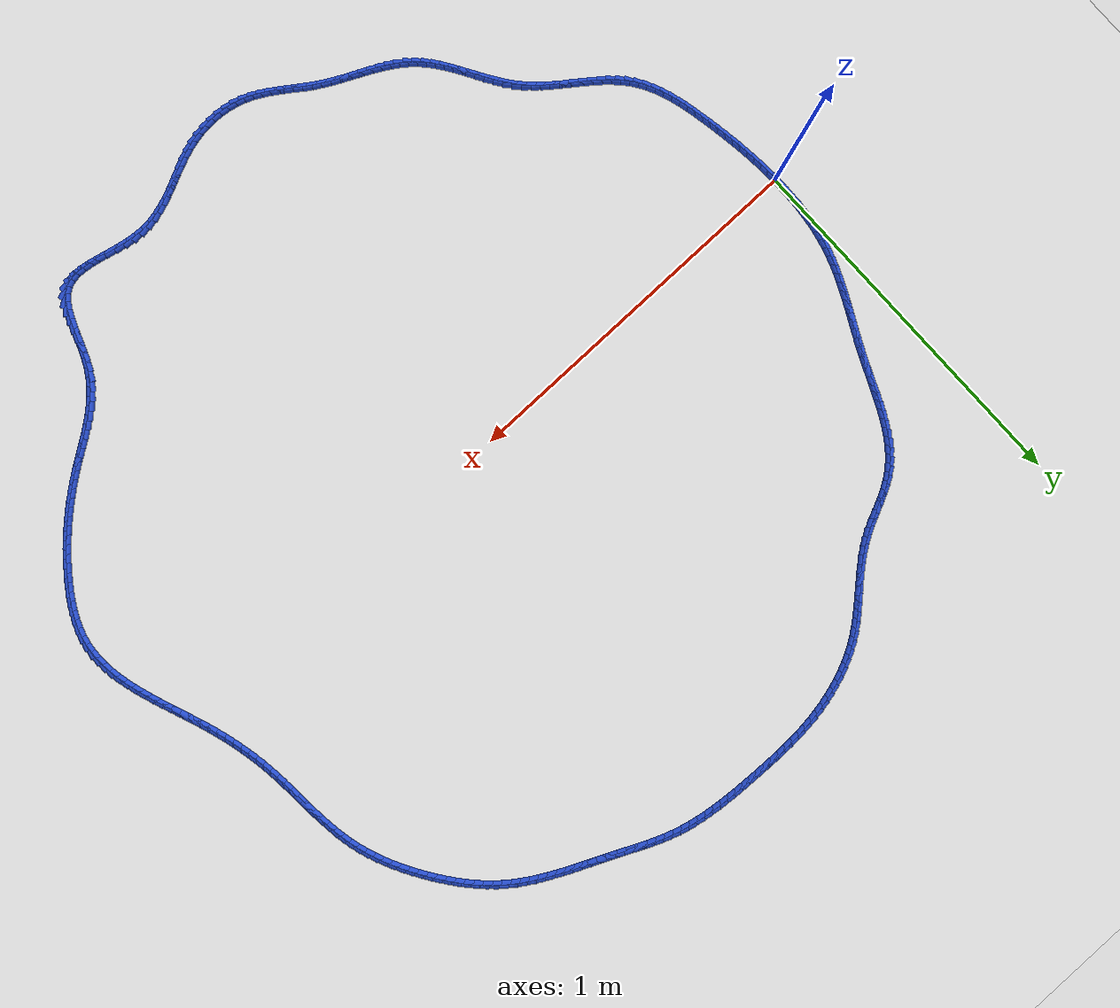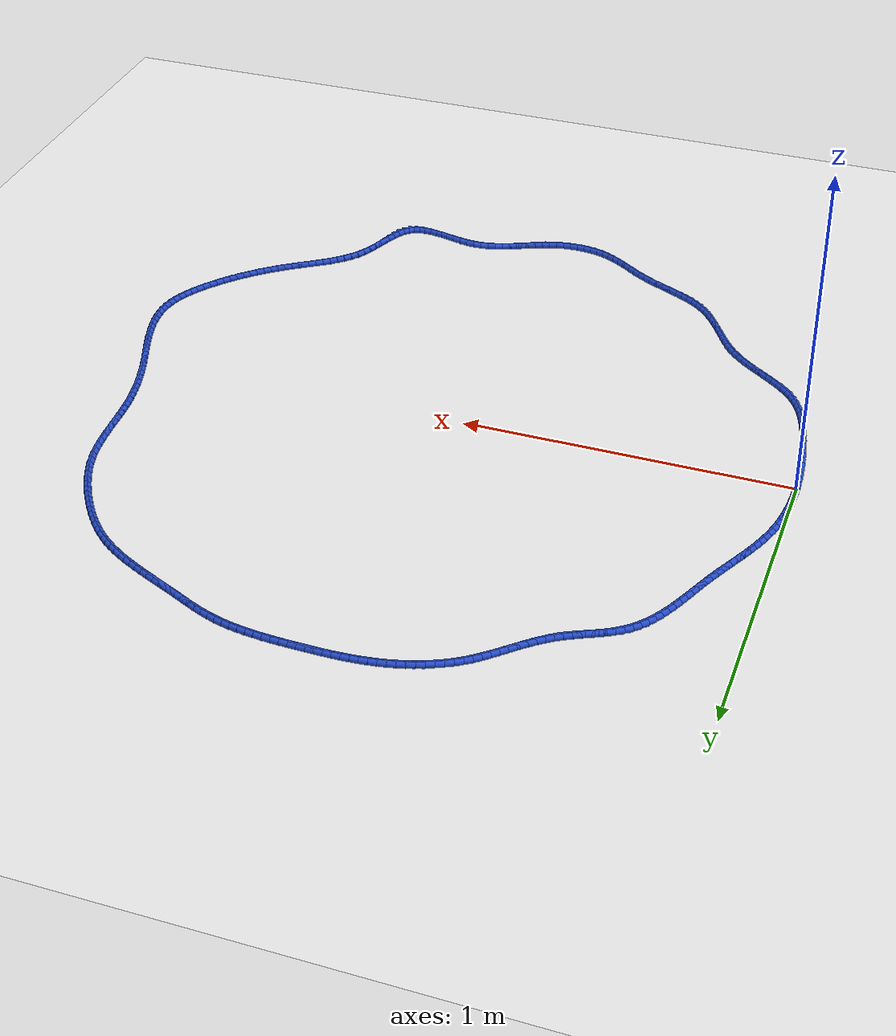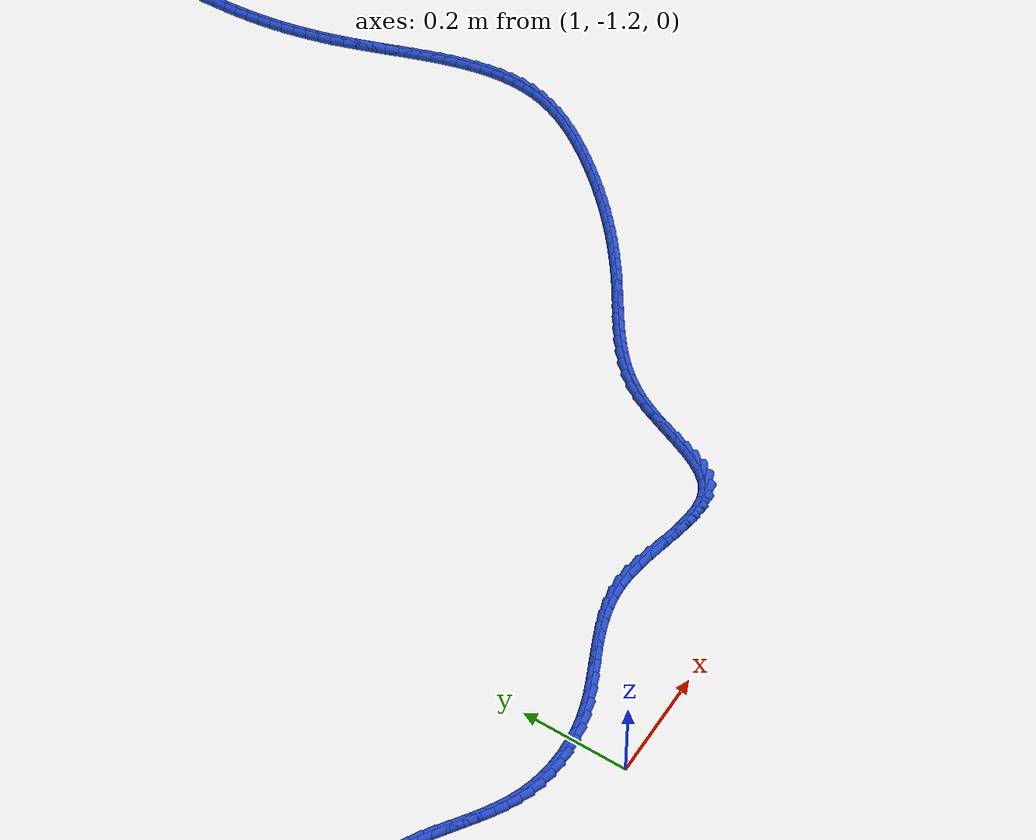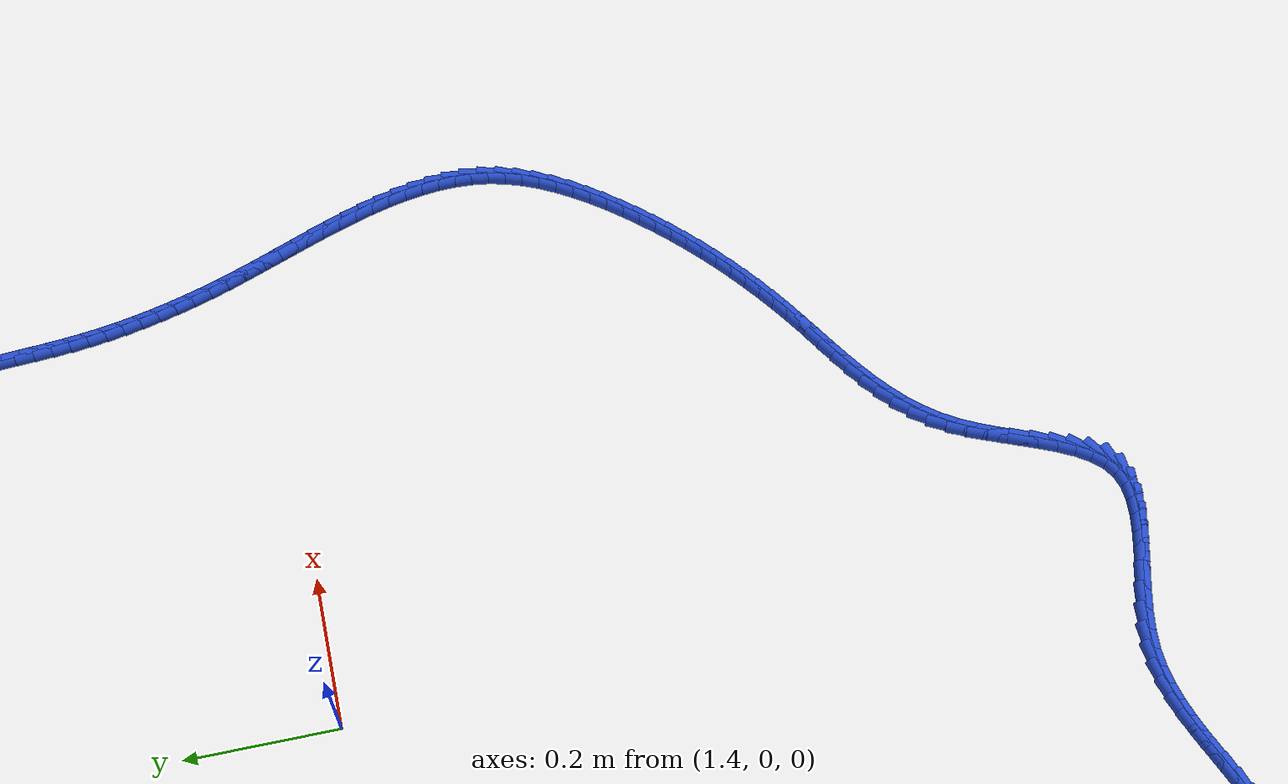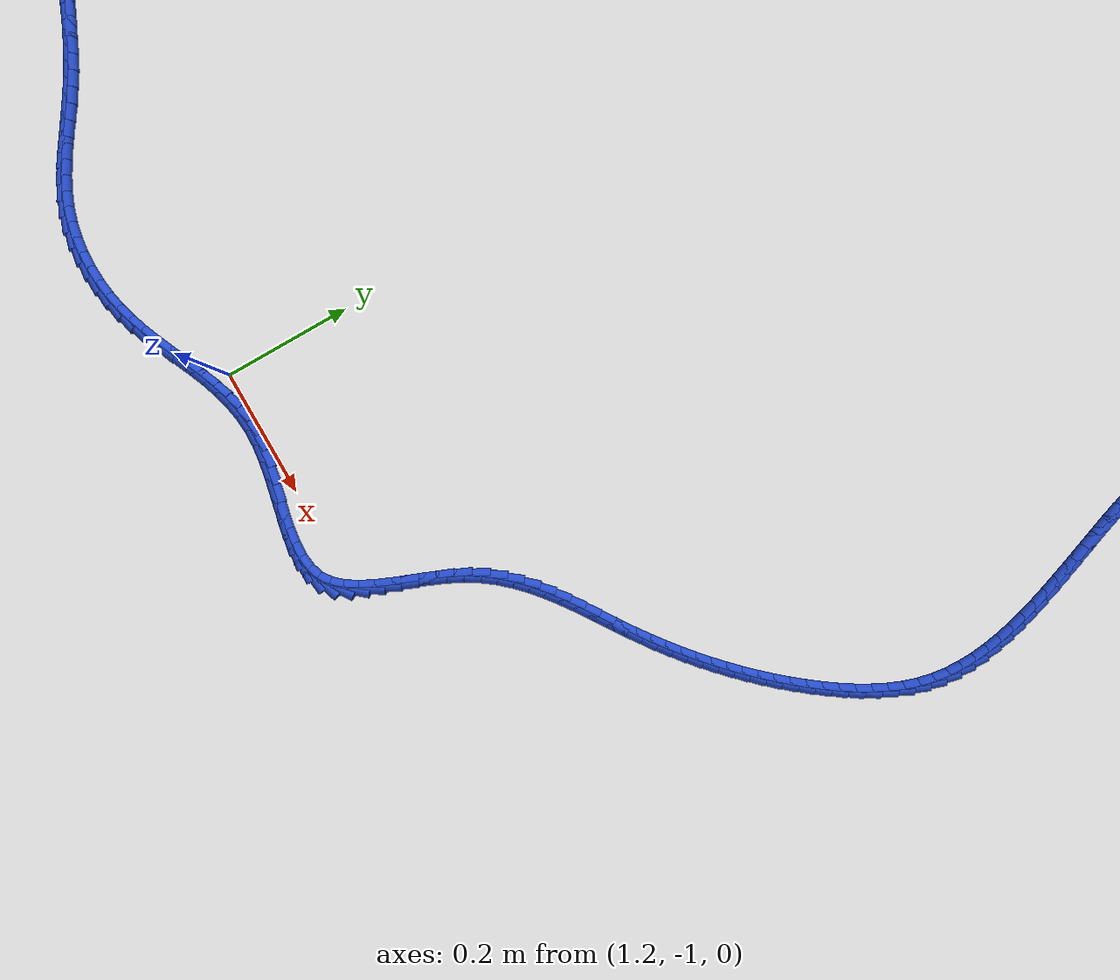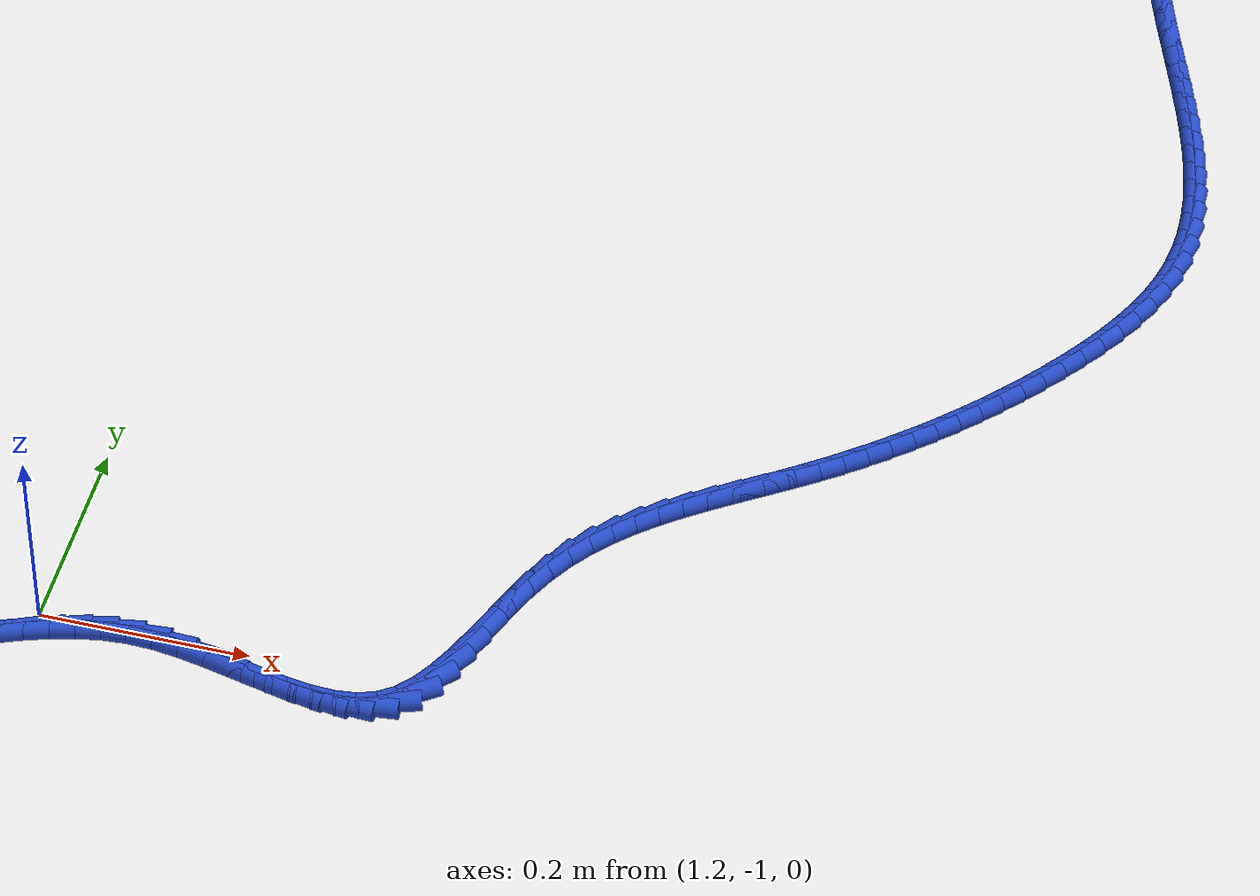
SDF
<sdf version="1.6">
 <world name="default">
  <light name="sun" type="directional">
   <pose>0 0 10 0 -0 0</pose>
   <diffuse>0.8 0.8 0.8 1</diffuse>
   <specular>0.2 0.2 0.2 1</specular>
   <attenuation>
    <range>1000</range>
    <constant>0.9</constant>
    <linear>0.01</linear>
    <quadratic>0.001</quadratic>
   </attenuation>
   <direction>-0.5 0.1 -0.9</direction>
  </light>
  <model name="ground_plane">
   <static>1</static>
   <link name="link">
    <collision name="collision">
     <geometry><plane><normal>0 0 1</normal><size>100 100</size></plane></geometry>
     <surface><friction><ode><mu>100</mu><mu2>50</mu2></ode></friction></surface>
    </collision>
    <visual name="visual">
     <cast_shadows>0</cast_shadows>
     <geometry><plane><normal>0 0 1</normal><size>100 100</size></plane></geometry>
     <material>
      <script><uri>file://media/materials/scripts/gazebo.material</uri><name>Gazebo/WhiteGlow</name></script>
     </material>
    </visual>
   </link>
  </model>
  <gravity>0 0 -9.8</gravity>
  <magnetic_field>6e-06 2.3e-05 -4.2e-05</magnetic_field>
  <atmosphere type="adiabatic"/>
  <physics name="default_physics" default="0" type="ode">
   <max_step_size>0.001</max_step_size>
   <real_time_factor>1</real_time_factor>
   <real_time_update_rate>1000</real_time_update_rate>
  </physics>
  <scene><ambient>0.4 0.4 0.4 1</ambient><background>0.7 0.7 0.7 1</background><shadows>1</shadows></scene>
  <spherical_coordinates>
   <surface_model>EARTH_WGS84</surface_model>
   <latitude_deg>0</latitude_deg>
   <longitude_deg>0</longitude_deg>
   <elevation>0</elevation>
   <heading_deg>0</heading_deg>
  </spherical_coordinates>
  <model name="line">
   <link name="link_0">
    <pose>4.336808689942018e-18 4.85722573273506e-17 0.01 0 1.57 -1.5600704985763028</pose>
    <collision name="collision">
     <geometry><cylinder><radius>0.01</radius><length>0.08</length></cylinder></geometry>
    </collision>
    <visual name="visual">
     <material>
      <script><name>Gazebo/Blue</name><uri>file://media/materials/scripts/gazebo.material</uri></script>
     </material>
     <geometry><cylinder><radius>0.01</radius><length>0.08</length></cylinder></geometry>
    </visual>
   </link>
   <link name="link_1">
    <pose>-0.0002594113208012447 0.02418474057067221 0.01 0 1.57 1.5566355840279211</pose>
    <collision name="collision">
     <geometry><cylinder><radius>0.01</radius><length>0.08</length></cylinder></geometry>
    </collision>
    <visual name="visual">
     <material>
      <script><name>Gazebo/Blue</name><uri>file://media/materials/scripts/gazebo.material</uri></script>
     </material>
     <geometry><cylinder><radius>0.01</radius><length>0.08</length></cylinder></geometry>
    </visual>
   </link>
   <link name="link_2">
    <pose>8.432898004426565e-05 0.048457289675787565 0.01 0 1.57 1.5299951298431929</pose>
    <collision name="collision">
     <geometry><cylinder><radius>0.01</radius><length>0.08</length></cylinder></geometry>
    </collision>
    <visual name="visual">
     <material>
      <script><name>Gazebo/Blue</name><uri>file://media/materials/scripts/gazebo.material</uri></script>
     </material>
     <geometry><cylinder><radius>0.01</radius><length>0.08</length></cylinder></geometry>
    </visual>
   </link>
   <link name="link_3">
    <pose>0.0010763455788256571 0.07275721539569707 0.01 0 1.57 1.5014542429999145</pose>
    <collision name="collision">
     <geometry><cylinder><radius>0.01</radius><length>0.08</length></cylinder></geometry>
    </collision>
    <visual name="visual">
     <material>
      <script><name>Gazebo/Blue</name><uri>file://media/materials/scripts/gazebo.material</uri></script>
     </material>
     <geometry><cylinder><radius>0.01</radius><length>0.08</length></cylinder></geometry>
    </visual>
   </link>
   <link name="link_4">
    <pose>0.0027617631518320586 0.0970240858107516 0.01 0 1.57 1.4708571564264772</pose>
    <collision name="collision">
     <geometry><cylinder><radius>0.01</radius><length>0.08</length></cylinder></geometry>
    </collision>
    <visual name="visual">
     <material>
      <script><name>Gazebo/Blue</name><uri>file://media/materials/scripts/gazebo.material</uri></script>
     </material>
     <geometry><cylinder><radius>0.01</radius><length>0.08</length></cylinder></geometry>
    </visual>
   </link>
   <link name="link_5">
    <pose>0.005185706375352599 0.12119746900130204 0.01 0 1.57 1.4380403393588337</pose>
    <collision name="collision">
     <geometry><cylinder><radius>0.01</radius><length>0.08</length></cylinder></geometry>
    </collision>
    <visual name="visual">
     <material>
      <script><name>Gazebo/Blue</name><uri>file://media/materials/scripts/gazebo.material</uri></script>
     </material>
     <geometry><cylinder><radius>0.01</radius><length>0.08</length></cylinder></geometry>
    </visual>
   </link>
   <link name="link_6">
    <pose>0.008393299925676398 0.14521693304769934 0.01 0 1.57 1.4028349200547487</pose>
    <collision name="collision">
     <geometry><cylinder><radius>0.01</radius><length>0.08</length></cylinder></geometry>
    </collision>
    <visual name="visual">
     <material>
      <script><name>Gazebo/Blue</name><uri>file://media/materials/scripts/gazebo.material</uri></script>
     </material>
     <geometry><cylinder><radius>0.01</radius><length>0.08</length></cylinder></geometry>
    </visual>
   </link>
   <link name="link_7">
    <pose>0.012429668479092586 0.1690220460302944 0.01 0 1.57 1.3650703853573645</pose>
    <collision name="collision">
     <geometry><cylinder><radius>0.01</radius><length>0.08</length></cylinder></geometry>
    </collision>
    <visual name="visual">
     <material>
      <script><name>Gazebo/Blue</name><uri>file://media/materials/scripts/gazebo.material</uri></script>
     </material>
     <geometry><cylinder><radius>0.01</radius><length>0.08</length></cylinder></geometry>
    </visual>
   </link>
   <link name="link_8">
    <pose>0.01733993671189029 0.19255237602943806 0.01 0 1.57 1.3245799037931814</pose>
    <collision name="collision">
     <geometry><cylinder><radius>0.01</radius><length>0.08</length></cylinder></geometry>
    </collision>
    <visual name="visual">
     <material>
      <script><name>Gazebo/Blue</name><uri>file://media/materials/scripts/gazebo.material</uri></script>
     </material>
     <geometry><cylinder><radius>0.01</radius><length>0.08</length></cylinder></geometry>
    </visual>
   </link>
   <link name="link_9">
    <pose>0.02316922930035863 0.21574749112548133 0.01 0 1.57 1.2816577159159306</pose>
    <collision name="collision">
     <geometry><cylinder><radius>0.01</radius><length>0.08</length></cylinder></geometry>
    </collision>
    <visual name="visual">
     <material>
      <script><name>Gazebo/Blue</name><uri>file://media/materials/scripts/gazebo.material</uri></script>
     </material>
     <geometry><cylinder><radius>0.01</radius><length>0.08</length></cylinder></geometry>
    </visual>
   </link>
   <link name="link_10">
    <pose>0.029953688595491558 0.23855431811630112 0.01 0 1.57 1.2408650860813086</pose>
    <collision name="collision">
     <geometry><cylinder><radius>0.01</radius><length>0.08</length></cylinder></geometry>
    </collision>
    <visual name="visual">
     <material>
      <script><name>Gazebo/Blue</name><uri>file://media/materials/scripts/gazebo.material</uri></script>
     </material>
     <geometry><cylinder><radius>0.01</radius><length>0.08</length></cylinder></geometry>
    </visual>
   </link>
   <link name="link_11">
    <pose>0.03763827852464199 0.26099448119070556 0.01 0 1.57 1.205128919519956</pose>
    <collision name="collision">
     <geometry><cylinder><radius>0.01</radius><length>0.08</length></cylinder></geometry>
    </collision>
    <visual name="visual">
     <material>
      <script><name>Gazebo/Blue</name><uri>file://media/materials/scripts/gazebo.material</uri></script>
     </material>
     <geometry><cylinder><radius>0.01</radius><length>0.08</length></cylinder></geometry>
    </visual>
   </link>
   <link name="link_12">
    <pose>0.04611487049312075 0.2831331002760352 0.01 0 1.57 1.1746962308401403</pose>
    <collision name="collision">
     <geometry><cylinder><radius>0.01</radius><length>0.08</length></cylinder></geometry>
    </collision>
    <visual name="visual">
     <material>
      <script><name>Gazebo/Blue</name><uri>file://media/materials/scripts/gazebo.material</uri></script>
     </material>
     <geometry><cylinder><radius>0.01</radius><length>0.08</length></cylinder></geometry>
    </visual>
   </link>
   <link name="link_13">
    <pose>0.055274676258217165 0.305035835712419 0.01 0 1.57 1.149680969126531</pose>
    <collision name="collision">
     <geometry><cylinder><radius>0.01</radius><length>0.08</length></cylinder></geometry>
    </collision>
    <visual name="visual">
     <material>
      <script><name>Gazebo/Blue</name><uri>file://media/materials/scripts/gazebo.material</uri></script>
     </material>
     <geometry><cylinder><radius>0.01</radius><length>0.08</length></cylinder></geometry>
    </visual>
   </link>
   <link name="link_14">
    <pose>0.0650089075772205 0.3267683478399855 0.01 0 1.57 1.1301209041413802</pose>
    <collision name="collision">
     <geometry><cylinder><radius>0.01</radius><length>0.08</length></cylinder></geometry>
    </collision>
    <visual name="visual">
     <material>
      <script><name>Gazebo/Blue</name><uri>file://media/materials/scripts/gazebo.material</uri></script>
     </material>
     <geometry><cylinder><radius>0.01</radius><length>0.08</length></cylinder></geometry>
    </visual>
   </link>
   <link name="link_15">
    <pose>0.07520877620742021 0.34839629699886393 0.01 0 1.57 1.1159995671180485</pose>
    <collision name="collision">
     <geometry><cylinder><radius>0.01</radius><length>0.08</length></cylinder></geometry>
    </collision>
    <visual name="visual">
     <material>
      <script><name>Gazebo/Blue</name><uri>file://media/materials/scripts/gazebo.material</uri></script>
     </material>
     <geometry><cylinder><radius>0.01</radius><length>0.08</length></cylinder></geometry>
    </visual>
   </link>
   <link name="link_16">
    <pose>0.08576549390610548 0.36998534352918255 0.01 0 1.57 1.10726432864977</pose>
    <collision name="collision">
     <geometry><cylinder><radius>0.01</radius><length>0.08</length></cylinder></geometry>
    </collision>
    <visual name="visual">
     <material>
      <script><name>Gazebo/Blue</name><uri>file://media/materials/scripts/gazebo.material</uri></script>
     </material>
     <geometry><cylinder><radius>0.01</radius><length>0.08</length></cylinder></geometry>
    </visual>
   </link>
   <link name="link_17">
    <pose>0.0965702724305657 0.3916011477710707 0.01 0 1.57 1.1038397107177151</pose>
    <collision name="collision">
     <geometry><cylinder><radius>0.01</radius><length>0.08</length></cylinder></geometry>
    </collision>
    <visual name="visual">
     <material>
      <script><name>Gazebo/Blue</name><uri>file://media/materials/scripts/gazebo.material</uri></script>
     </material>
     <geometry><cylinder><radius>0.01</radius><length>0.08</length></cylinder></geometry>
    </visual>
   </link>
   <link name="link_18">
    <pose>0.10751432353809012 0.4133093700646566 0.01 0 1.57 1.1056357497975802</pose>
    <collision name="collision">
     <geometry><cylinder><radius>0.01</radius><length>0.08</length></cylinder></geometry>
    </collision>
    <visual name="visual">
     <material>
      <script><name>Gazebo/Blue</name><uri>file://media/materials/scripts/gazebo.material</uri></script>
     </material>
     <geometry><cylinder><radius>0.01</radius><length>0.08</length></cylinder></geometry>
    </visual>
   </link>
   <link name="link_19">
    <pose>0.11848885898596817 0.43517567075006963 0.01 0 1.57 1.1125516474508779</pose>
    <collision name="collision">
     <geometry><cylinder><radius>0.01</radius><length>0.08</length></cylinder></geometry>
    </collision>
    <visual name="visual">
     <material>
      <script><name>Gazebo/Blue</name><uri>file://media/materials/scripts/gazebo.material</uri></script>
     </material>
     <geometry><cylinder><radius>0.01</radius><length>0.08</length></cylinder></geometry>
    </visual>
   </link>
   <link name="link_20">
    <pose>0.12938509053148908 0.4572657101674382 0.01 0 1.57 1.1244751622478417</pose>
    <collision name="collision">
     <geometry><cylinder><radius>0.01</radius><length>0.08</length></cylinder></geometry>
    </collision>
    <visual name="visual">
     <material>
      <script><name>Gazebo/Blue</name><uri>file://media/materials/scripts/gazebo.material</uri></script>
     </material>
     <geometry><cylinder><radius>0.01</radius><length>0.08</length></cylinder></geometry>
    </visual>
   </link>
   <link name="link_21">
    <pose>0.1400942299319422 0.47964514865689134 0.01 0 1.57 1.140698608995218</pose>
    <collision name="collision">
     <geometry><cylinder><radius>0.01</radius><length>0.08</length></cylinder></geometry>
    </collision>
    <visual name="visual">
     <material>
      <script><name>Gazebo/Blue</name><uri>file://media/materials/scripts/gazebo.material</uri></script>
     </material>
     <geometry><cylinder><radius>0.01</radius><length>0.08</length></cylinder></geometry>
    </visual>
   </link>
   <link name="link_22">
    <pose>0.15051884595879075 0.5023696373357445 0.01 0 1.57 1.1538595059746448</pose>
    <collision name="collision">
     <geometry><cylinder><radius>0.01</radius><length>0.08</length></cylinder></geometry>
    </collision>
    <visual name="visual">
     <material>
      <script><name>Gazebo/Blue</name><uri>file://media/materials/scripts/gazebo.material</uri></script>
     </material>
     <geometry><cylinder><radius>0.01</radius><length>0.08</length></cylinder></geometry>
    </visual>
   </link>
   <link name="link_23">
    <pose>0.16070504473985237 0.5253683242316982 0.01 0 1.57 1.159137282129465</pose>
    <collision name="collision">
     <geometry><cylinder><radius>0.01</radius><length>0.08</length></cylinder></geometry>
    </collision>
    <visual name="visual">
     <material>
      <script><name>Gazebo/Blue</name><uri>file://media/materials/scripts/gazebo.material</uri></script>
     </material>
     <geometry><cylinder><radius>0.01</radius><length>0.08</length></cylinder></geometry>
    </visual>
   </link>
   <link name="link_24">
    <pose>0.17079731385656666 0.5484836513179461 0.01 0 1.57 1.1565526897229124</pose>
    <collision name="collision">
     <geometry><cylinder><radius>0.01</radius><length>0.08</length></cylinder></geometry>
    </collision>
    <visual name="visual">
     <material>
      <script><name>Gazebo/Blue</name><uri>file://media/materials/scripts/gazebo.material</uri></script>
     </material>
     <geometry><cylinder><radius>0.01</radius><length>0.08</length></cylinder></geometry>
    </visual>
   </link>
   <link name="link_25">
    <pose>0.1809420608020265 0.5715563685011549 0.01 0 1.57 1.146062453418453</pose>
    <collision name="collision">
     <geometry><cylinder><radius>0.01</radius><length>0.08</length></cylinder></geometry>
    </collision>
    <visual name="visual">
     <material>
      <script><name>Gazebo/Blue</name><uri>file://media/materials/scripts/gazebo.material</uri></script>
     </material>
     <geometry><cylinder><radius>0.01</radius><length>0.08</length></cylinder></geometry>
    </visual>
   </link>
   <link name="link_26">
    <pose>0.19128569306932497 0.594427225687992 0.01 0 1.57 1.1274641606894484</pose>
    <collision name="collision">
     <geometry><cylinder><radius>0.01</radius><length>0.08</length></cylinder></geometry>
    </collision>
    <visual name="visual">
     <material>
      <script><name>Gazebo/Blue</name><uri>file://media/materials/scripts/gazebo.material</uri></script>
     </material>
     <geometry><cylinder><radius>0.01</radius><length>0.08</length></cylinder></geometry>
    </visual>
   </link>
   <link name="link_27">
    <pose>0.20197461815155496 0.616936972785124 0.01 0 1.57 1.1004071970711633</pose>
    <collision name="collision">
     <geometry><cylinder><radius>0.01</radius><length>0.08</length></cylinder></geometry>
    </collision>
    <visual name="visual">
     <material>
      <script><name>Gazebo/Blue</name><uri>file://media/materials/scripts/gazebo.material</uri></script>
     </material>
     <geometry><cylinder><radius>0.01</radius><length>0.08</length></cylinder></geometry>
    </visual>
   </link>
   <link name="link_28">
    <pose>0.2131552435418096 0.6389263596992186 0.01 0 1.57 1.0644164259000384</pose>
    <collision name="collision">
     <geometry><cylinder><radius>0.01</radius><length>0.08</length></cylinder></geometry>
    </collision>
    <visual name="visual">
     <material>
      <script><name>Gazebo/Blue</name><uri>file://media/materials/scripts/gazebo.material</uri></script>
     </material>
     <geometry><cylinder><radius>0.01</radius><length>0.08</length></cylinder></geometry>
    </visual>
   </link>
   <link name="link_29">
    <pose>0.2249739767331818 0.6602361363369424 0.01 0 1.57 1.0189372276397004</pose>
    <collision name="collision">
     <geometry><cylinder><radius>0.01</radius><length>0.08</length></cylinder></geometry>
    </collision>
    <visual name="visual">
     <material>
      <script><name>Gazebo/Blue</name><uri>file://media/materials/scripts/gazebo.material</uri></script>
     </material>
     <geometry><cylinder><radius>0.01</radius><length>0.08</length></cylinder></geometry>
    </visual>
   </link>
   <link name="link_30">
    <pose>0.23757722521876468 0.6807070526049627 0.01 0 1.57 0.9634141751349451</pose>
    <collision name="collision">
     <geometry><cylinder><radius>0.01</radius><length>0.08</length></cylinder></geometry>
    </collision>
    <visual name="visual">
     <material>
      <script><name>Gazebo/Blue</name><uri>file://media/materials/scripts/gazebo.material</uri></script>
     </material>
     <geometry><cylinder><radius>0.01</radius><length>0.08</length></cylinder></geometry>
    </visual>
   </link>
   <link name="link_31">
    <pose>0.2511113964916511 0.7001798584099466 0.01 0 1.57 0.8974169943597563</pose>
    <collision name="collision">
     <geometry><cylinder><radius>0.01</radius><length>0.08</length></cylinder></geometry>
    </collision>
    <visual name="visual">
     <material>
      <script><name>Gazebo/Blue</name><uri>file://media/materials/scripts/gazebo.material</uri></script>
     </material>
     <geometry><cylinder><radius>0.01</radius><length>0.08</length></cylinder></geometry>
    </visual>
   </link>
   <link name="link_32">
    <pose>0.2657228980449341 0.7184953036585606 0.01 0 1.57 0.8208219893452217</pose>
    <collision name="collision">
     <geometry><cylinder><radius>0.01</radius><length>0.08</length></cylinder></geometry>
    </collision>
    <visual name="visual">
     <material>
      <script><name>Gazebo/Blue</name><uri>file://media/materials/scripts/gazebo.material</uri></script>
     </material>
     <geometry><cylinder><radius>0.01</radius><length>0.08</length></cylinder></geometry>
    </visual>
   </link>
   <link name="link_33">
    <pose>0.2815581373717067 0.7354941382574725 0.01 0 1.57 0.7340380819048063</pose>
    <collision name="collision">
     <geometry><cylinder><radius>0.01</radius><length>0.08</length></cylinder></geometry>
    </collision>
    <visual name="visual">
     <material>
      <script><name>Gazebo/Blue</name><uri>file://media/materials/scripts/gazebo.material</uri></script>
     </material>
     <geometry><cylinder><radius>0.01</radius><length>0.08</length></cylinder></geometry>
    </visual>
   </link>
   <link name="link_34">
    <pose>0.29876352196506195 0.7510171121133489 0.01 0 1.57 0.6395126139656503</pose>
    <collision name="collision">
     <geometry><cylinder><radius>0.01</radius><length>0.08</length></cylinder></geometry>
    </collision>
    <visual name="visual">
     <material>
      <script><name>Gazebo/Blue</name><uri>file://media/materials/scripts/gazebo.material</uri></script>
     </material>
     <geometry><cylinder><radius>0.01</radius><length>0.08</length></cylinder></geometry>
    </visual>
   </link>
   <link name="link_35">
    <pose>0.3174657678247337 0.76492759067717 0.01 0 1.57 0.5566670696537142</pose>
    <collision name="collision">
     <geometry><cylinder><radius>0.01</radius><length>0.08</length></cylinder></geometry>
    </collision>
    <visual name="visual">
     <material>
      <script><name>Gazebo/Blue</name><uri>file://media/materials/scripts/gazebo.material</uri></script>
     </material>
     <geometry><cylinder><radius>0.01</radius><length>0.08</length></cylinder></geometry>
    </visual>
   </link>
   <link name="link_36">
    <pose>0.3375161573066096 0.7774052730402388 0.01 0 1.57 0.4985039872697097</pose>
    <collision name="collision">
     <geometry><cylinder><radius>0.01</radius><length>0.08</length></cylinder></geometry>
    </collision>
    <visual name="visual">
     <material>
      <script><name>Gazebo/Blue</name><uri>file://media/materials/scripts/gazebo.material</uri></script>
     </material>
     <geometry><cylinder><radius>0.01</radius><length>0.08</length></cylinder></geometry>
    </visual>
   </link>
   <link name="link_37">
    <pose>0.358563357671173 0.788862560333518 0.01 0 1.57 0.4640420527576995</pose>
    <collision name="collision">
     <geometry><cylinder><radius>0.01</radius><length>0.08</length></cylinder></geometry>
    </collision>
    <visual name="visual">
     <material>
      <script><name>Gazebo/Blue</name><uri>file://media/materials/scripts/gazebo.material</uri></script>
     </material>
     <geometry><cylinder><radius>0.01</radius><length>0.08</length></cylinder></geometry>
    </visual>
   </link>
   <link name="link_38">
    <pose>0.38025134015018414 0.7997172470445698 0.01 0 1.57 0.4520584453697039</pose>
    <collision name="collision">
     <geometry><cylinder><radius>0.01</radius><length>0.08</length></cylinder></geometry>
    </collision>
    <visual name="visual">
     <material>
      <script><name>Gazebo/Blue</name><uri>file://media/materials/scripts/gazebo.material</uri></script>
     </material>
     <geometry><cylinder><radius>0.01</radius><length>0.08</length></cylinder></geometry>
    </visual>
   </link>
   <link name="link_39">
    <pose>0.4022240759754039 0.810387127660957 0.01 0 1.57 0.4618978438068161</pose>
    <collision name="collision">
     <geometry><cylinder><radius>0.01</radius><length>0.08</length></cylinder></geometry>
    </collision>
    <visual name="visual">
     <material>
      <script><name>Gazebo/Blue</name><uri>file://media/materials/scripts/gazebo.material</uri></script>
     </material>
     <geometry><cylinder><radius>0.01</radius><length>0.08</length></cylinder></geometry>
    </visual>
   </link>
   <link name="link_40">
    <pose>0.42412553637859246 0.8212899966702415 0.01 0 1.57 0.49360357574029795</pose>
    <collision name="collision">
     <geometry><cylinder><radius>0.01</radius><length>0.08</length></cylinder></geometry>
    </collision>
    <visual name="visual">
     <material>
      <script><name>Gazebo/Blue</name><uri>file://media/materials/scripts/gazebo.material</uri></script>
     </material>
     <geometry><cylinder><radius>0.01</radius><length>0.08</length></cylinder></geometry>
    </visual>
   </link>
   <link name="link_41">
    <pose>0.44559969259151044 0.8328436485599858 0.01 0 1.57 0.5472585258388312</pose>
    <collision name="collision">
     <geometry><cylinder><radius>0.01</radius><length>0.08</length></cylinder></geometry>
    </collision>
    <visual name="visual">
     <material>
      <script><name>Gazebo/Blue</name><uri>file://media/materials/scripts/gazebo.material</uri></script>
     </material>
     <geometry><cylinder><radius>0.01</radius><length>0.08</length></cylinder></geometry>
    </visual>
   </link>
   <link name="link_42">
    <pose>0.46629839323533473 0.8454561853802485 0.01 0 1.57 0.6081778418072382</pose>
    <collision name="collision">
     <geometry><cylinder><radius>0.01</radius><length>0.08</length></cylinder></geometry>
    </collision>
    <visual name="visual">
     <material>
      <script><name>Gazebo/Blue</name><uri>file://media/materials/scripts/gazebo.material</uri></script>
     </material>
     <geometry><cylinder><radius>0.01</radius><length>0.08</length></cylinder></geometry>
    </visual>
   </link>
   <link name="link_43">
    <pose>0.48610765157447816 0.8592475901037856 0.01 0 1.57 0.6585960491223576</pose>
    <collision name="collision">
     <geometry><cylinder><radius>0.01</radius><length>0.08</length></cylinder></geometry>
    </collision>
    <visual name="visual">
     <material>
      <script><name>Gazebo/Blue</name><uri>file://media/materials/scripts/gazebo.material</uri></script>
     </material>
     <geometry><cylinder><radius>0.01</radius><length>0.08</length></cylinder></geometry>
    </visual>
   </link>
   <link name="link_44">
    <pose>0.5051815179751064 0.8740080495335601 0.01 0 1.57 0.6972504487326401</pose>
    <collision name="collision">
     <geometry><cylinder><radius>0.01</radius><length>0.08</length></cylinder></geometry>
    </collision>
    <visual name="visual">
     <material>
      <script><name>Gazebo/Blue</name><uri>file://media/materials/scripts/gazebo.material</uri></script>
     </material>
     <geometry><cylinder><radius>0.01</radius><length>0.08</length></cylinder></geometry>
    </visual>
   </link>
   <link name="link_45">
    <pose>0.5236887334696474 0.8895096748948148 0.01 0 1.57 0.7240991831613288</pose>
    <collision name="collision">
     <geometry><cylinder><radius>0.01</radius><length>0.08</length></cylinder></geometry>
    </collision>
    <visual name="visual">
     <material>
      <script><name>Gazebo/Blue</name><uri>file://media/materials/scripts/gazebo.material</uri></script>
     </material>
     <geometry><cylinder><radius>0.01</radius><length>0.08</length></cylinder></geometry>
    </visual>
   </link>
   <link name="link_46">
    <pose>0.5417980390905297 0.9055245774127907 0.01 0 1.57 0.7392102603522721</pose>
    <collision name="collision">
     <geometry><cylinder><radius>0.01</radius><length>0.08</length></cylinder></geometry>
    </collision>
    <visual name="visual">
     <material>
      <script><name>Gazebo/Blue</name><uri>file://media/materials/scripts/gazebo.material</uri></script>
     </material>
     <geometry><cylinder><radius>0.01</radius><length>0.08</length></cylinder></geometry>
    </visual>
   </link>
   <link name="link_47">
    <pose>0.559678175870181 0.9218248683127298 0.01 0 1.57 0.7426499264429451</pose>
    <collision name="collision">
     <geometry><cylinder><radius>0.01</radius><length>0.08</length></cylinder></geometry>
    </collision>
    <visual name="visual">
     <material>
      <script><name>Gazebo/Blue</name><uri>file://media/materials/scripts/gazebo.material</uri></script>
     </material>
     <geometry><cylinder><radius>0.01</radius><length>0.08</length></cylinder></geometry>
    </visual>
   </link>
   <link name="link_48">
    <pose>0.5774978848410298 0.9381826588198747 0.01 0 1.57 0.7344208447195194</pose>
    <collision name="collision">
     <geometry><cylinder><radius>0.01</radius><length>0.08</length></cylinder></geometry>
    </collision>
    <visual name="visual">
     <material>
      <script><name>Gazebo/Blue</name><uri>file://media/materials/scripts/gazebo.material</uri></script>
     </material>
     <geometry><cylinder><radius>0.01</radius><length>0.08</length></cylinder></geometry>
    </visual>
   </link>
   <link name="link_49">
    <pose>0.5954259070355041 0.954370060159466 0.01 0 1.57 0.714447890086851</pose>
    <collision name="collision">
     <geometry><cylinder><radius>0.01</radius><length>0.08</length></cylinder></geometry>
    </collision>
    <visual name="visual">
     <material>
      <script><name>Gazebo/Blue</name><uri>file://media/materials/scripts/gazebo.material</uri></script>
     </material>
     <geometry><cylinder><radius>0.01</radius><length>0.08</length></cylinder></geometry>
    </visual>
   </link>
   <link name="link_50">
    <pose>0.6136309834860321 0.9701591835567466 0.01 0 1.57 0.6826111355652248</pose>
    <collision name="collision">
     <geometry><cylinder><radius>0.01</radius><length>0.08</length></cylinder></geometry>
    </collision>
    <visual name="visual">
     <material>
      <script><name>Gazebo/Blue</name><uri>file://media/materials/scripts/gazebo.material</uri></script>
     </material>
     <geometry><cylinder><radius>0.01</radius><length>0.08</length></cylinder></geometry>
    </visual>
   </link>
   <link name="link_51">
    <pose>0.6322818552250419 0.9853221402369577 0.01 0 1.57 0.6388288600864945</pose>
    <collision name="collision">
     <geometry><cylinder><radius>0.01</radius><length>0.08</length></cylinder></geometry>
    </collision>
    <visual name="visual">
     <material>
      <script><name>Gazebo/Blue</name><uri>file://media/materials/scripts/gazebo.material</uri></script>
     </material>
     <geometry><cylinder><radius>0.01</radius><length>0.08</length></cylinder></geometry>
    </visual>
   </link>
   <link name="link_52">
    <pose>0.6515472632849617 0.9996310414253418 0.01 0 1.57 0.5837840654750404</pose>
    <collision name="collision">
     <geometry><cylinder><radius>0.01</radius><length>0.08</length></cylinder></geometry>
    </collision>
    <visual name="visual">
     <material>
      <script><name>Gazebo/Blue</name><uri>file://media/materials/scripts/gazebo.material</uri></script>
     </material>
     <geometry><cylinder><radius>0.01</radius><length>0.08</length></cylinder></geometry>
    </visual>
   </link>
   <link name="link_53">
    <pose>0.6715857114225281 1.0128682454057343 0.01 0 1.57 0.5258936320840149</pose>
    <collision name="collision">
     <geometry><cylinder><radius>0.01</radius><length>0.08</length></cylinder></geometry>
    </collision>
    <visual name="visual">
     <material>
      <script><name>Gazebo/Blue</name><uri>file://media/materials/scripts/gazebo.material</uri></script>
     </material>
     <geometry><cylinder><radius>0.01</radius><length>0.08</length></cylinder></geometry>
    </visual>
   </link>
   <link name="link_54">
    <pose>0.6924144240672523 1.0249575247979672 0.01 0 1.57 0.47110887614652663</pose>
    <collision name="collision">
     <geometry><cylinder><radius>0.01</radius><length>0.08</length></cylinder></geometry>
    </collision>
    <visual name="visual">
     <material>
      <script><name>Gazebo/Blue</name><uri>file://media/materials/scripts/gazebo.material</uri></script>
     </material>
     <geometry><cylinder><radius>0.01</radius><length>0.08</length></cylinder></geometry>
    </visual>
   </link>
   <link name="link_55">
    <pose>0.7139476508497763 1.0359257254250915 0.01 0 1.57 0.4194306270549513</pose>
    <collision name="collision">
     <geometry><cylinder><radius>0.01</radius><length>0.08</length></cylinder></geometry>
    </collision>
    <visual name="visual">
     <material>
      <script><name>Gazebo/Blue</name><uri>file://media/materials/scripts/gazebo.material</uri></script>
     </material>
     <geometry><cylinder><radius>0.01</radius><length>0.08</length></cylinder></geometry>
    </visual>
   </link>
   <link name="link_56">
    <pose>0.7360973060315656 1.045802030711054 0.01 0 1.57 0.37067570156111307</pose>
    <collision name="collision">
     <geometry><cylinder><radius>0.01</radius><length>0.08</length></cylinder></geometry>
    </collision>
    <visual name="visual">
     <material>
      <script><name>Gazebo/Blue</name><uri>file://media/materials/scripts/gazebo.material</uri></script>
     </material>
     <geometry><cylinder><radius>0.01</radius><length>0.08</length></cylinder></geometry>
    </visual>
   </link>
   <link name="link_57">
    <pose>0.7587753038740852 1.0546156240797993 0.01 0 1.57 0.32462784409352474</pose>
    <collision name="collision">
     <geometry><cylinder><radius>0.01</radius><length>0.08</length></cylinder></geometry>
    </collision>
    <visual name="visual">
     <material>
      <script><name>Gazebo/Blue</name><uri>file://media/materials/scripts/gazebo.material</uri></script>
     </material>
     <geometry><cylinder><radius>0.01</radius><length>0.08</length></cylinder></geometry>
    </visual>
   </link>
   <link name="link_58">
    <pose>0.7818935586388001 1.0623956889552728 0.01 0 1.57 0.28105029638302537</pose>
    <collision name="collision">
     <geometry><cylinder><radius>0.01</radius><length>0.08</length></cylinder></geometry>
    </collision>
    <visual name="visual">
     <material>
      <script><name>Gazebo/Blue</name><uri>file://media/materials/scripts/gazebo.material</uri></script>
     </material>
     <geometry><cylinder><radius>0.01</radius><length>0.08</length></cylinder></geometry>
    </visual>
   </link>
   <link name="link_59">
    <pose>0.8053639845871757 1.0691714087614197 0.01 0 1.57 0.23969495085195333</pose>
    <collision name="collision">
     <geometry><cylinder><radius>0.01</radius><length>0.08</length></cylinder></geometry>
    </collision>
    <visual name="visual">
     <material>
      <script><name>Gazebo/Blue</name><uri>file://media/materials/scripts/gazebo.material</uri></script>
     </material>
     <geometry><cylinder><radius>0.01</radius><length>0.08</length></cylinder></geometry>
    </visual>
   </link>
   <link name="link_60">
    <pose>0.829098495980677 1.0749719669221856 0.01 0 1.57 0.20030847614131383</pose>
    <collision name="collision">
     <geometry><cylinder><radius>0.01</radius><length>0.08</length></cylinder></geometry>
    </collision>
    <visual name="visual">
     <material>
      <script><name>Gazebo/Blue</name><uri>file://media/materials/scripts/gazebo.material</uri></script>
     </material>
     <geometry><cylinder><radius>0.01</radius><length>0.08</length></cylinder></geometry>
    </visual>
   </link>
   <link name="link_61">
    <pose>0.853009007080769 1.0798265468615158 0.01 0 1.57 0.16263588340952698</pose>
    <collision name="collision">
     <geometry><cylinder><radius>0.01</radius><length>0.08</length></cylinder></geometry>
    </collision>
    <visual name="visual">
     <material>
      <script><name>Gazebo/Blue</name><uri>file://media/materials/scripts/gazebo.material</uri></script>
     </material>
     <geometry><cylinder><radius>0.01</radius><length>0.08</length></cylinder></geometry>
    </visual>
   </link>
   <link name="link_62">
    <pose>0.8770074321489171 1.0837643320033559 0.01 0 1.57 0.12665063717586408</pose>
    <collision name="collision">
     <geometry><cylinder><radius>0.01</radius><length>0.08</length></cylinder></geometry>
    </collision>
    <visual name="visual">
     <material>
      <script><name>Gazebo/Blue</name><uri>file://media/materials/scripts/gazebo.material</uri></script>
     </material>
     <geometry><cylinder><radius>0.01</radius><length>0.08</length></cylinder></geometry>
    </visual>
   </link>
   <link name="link_63">
    <pose>0.901015671403718 1.086821353574677 0.01 0 1.57 0.09371812829061692</pose>
    <collision name="collision">
     <geometry><cylinder><radius>0.01</radius><length>0.08</length></cylinder></geometry>
    </collision>
    <visual name="visual">
     <material>
      <script><name>Gazebo/Blue</name><uri>file://media/materials/scripts/gazebo.material</uri></script>
     </material>
     <geometry><cylinder><radius>0.01</radius><length>0.08</length></cylinder></geometry>
    </visual>
   </link>
   <link name="link_64">
    <pose>0.9250196896062849 1.0890775746321515 0.01 0 1.57 0.06457753009806019</pose>
    <collision name="collision">
     <geometry><cylinder><radius>0.01</radius><length>0.08</length></cylinder></geometry>
    </collision>
    <visual name="visual">
     <material>
      <script><name>Gazebo/Blue</name><uri>file://media/materials/scripts/gazebo.material</uri></script>
     </material>
     <geometry><cylinder><radius>0.01</radius><length>0.08</length></cylinder></geometry>
    </visual>
   </link>
   <link name="link_65">
    <pose>0.9490307534528659 1.0906303088645148 0.01 0 1.57 0.039373140795397464</pose>
    <collision name="collision">
     <geometry><cylinder><radius>0.01</radius><length>0.08</length></cylinder></geometry>
    </collision>
    <visual name="visual">
     <material>
      <script><name>Gazebo/Blue</name><uri>file://media/materials/scripts/gazebo.material</uri></script>
     </material>
     <geometry><cylinder><radius>0.01</radius><length>0.08</length></cylinder></geometry>
    </visual>
   </link>
   <link name="link_66">
    <pose>0.9730601917125367 1.091576912526526 0.01 0 1.57 0.018196036847997997</pose>
    <collision name="collision">
     <geometry><cylinder><radius>0.01</radius><length>0.08</length></cylinder></geometry>
    </collision>
    <visual name="visual">
     <material>
      <script><name>Gazebo/Blue</name><uri>file://media/materials/scripts/gazebo.material</uri></script>
     </material>
     <geometry><cylinder><radius>0.01</radius><length>0.08</length></cylinder></geometry>
    </visual>
   </link>
   <link name="link_67">
    <pose>0.9971193331543736 1.0920147418729458 0.01 0 1.57 0.0010958956428662179</pose>
    <collision name="collision">
     <geometry><cylinder><radius>0.01</radius><length>0.08</length></cylinder></geometry>
    </collision>
    <visual name="visual">
     <material>
      <script><name>Gazebo/Blue</name><uri>file://media/materials/scripts/gazebo.material</uri></script>
     </material>
     <geometry><cylinder><radius>0.01</radius><length>0.08</length></cylinder></geometry>
    </visual>
   </link>
   <link name="link_68">
    <pose>1.0212195065474527 1.0920411531585328 0.01 0 1.57 -0.01190918186807699</pose>
    <collision name="collision">
     <geometry><cylinder><radius>0.01</radius><length>0.08</length></cylinder></geometry>
    </collision>
    <visual name="visual">
     <material>
      <script><name>Gazebo/Blue</name><uri>file://media/materials/scripts/gazebo.material</uri></script>
     </material>
     <geometry><cylinder><radius>0.01</radius><length>0.08</length></cylinder></geometry>
    </visual>
   </link>
   <link name="link_69">
    <pose>1.045372040660851 1.091753502638048 0.01 0 1.57 -0.020824186868915316</pose>
    <collision name="collision">
     <geometry><cylinder><radius>0.01</radius><length>0.08</length></cylinder></geometry>
    </collision>
    <visual name="visual">
     <material>
      <script><name>Gazebo/Blue</name><uri>file://media/materials/scripts/gazebo.material</uri></script>
     </material>
     <geometry><cylinder><radius>0.01</radius><length>0.08</length></cylinder></geometry>
    </visual>
   </link>
   <link name="link_70">
    <pose>1.0695882642636443 1.091249146566251 0.01 0 1.57 -0.026765653244638928</pose>
    <collision name="collision">
     <geometry><cylinder><radius>0.01</radius><length>0.08</length></cylinder></geometry>
    </collision>
    <visual name="visual">
     <material>
      <script><name>Gazebo/Blue</name><uri>file://media/materials/scripts/gazebo.material</uri></script>
     </material>
     <geometry><cylinder><radius>0.01</radius><length>0.08</length></cylinder></geometry>
    </visual>
   </link>
   <link name="link_71">
    <pose>1.0938724663864265 1.0905990087725475 0.01 0 1.57 -0.03485059119270547</pose>
    <collision name="collision">
     <geometry><cylinder><radius>0.01</radius><length>0.08</length></cylinder></geometry>
    </collision>
    <visual name="visual">
     <material>
      <script><name>Gazebo/Blue</name><uri>file://media/materials/scripts/gazebo.material</uri></script>
     </material>
     <geometry><cylinder><radius>0.01</radius><length>0.08</length></cylinder></geometry>
    </visual>
   </link>
   <link name="link_72">
    <pose>1.118196166064458 1.0897509700986394 0.01 0 1.57 -0.046577803580105076</pose>
    <collision name="collision">
     <geometry><cylinder><radius>0.01</radius><length>0.08</length></cylinder></geometry>
    </collision>
    <visual name="visual">
     <material>
      <script><name>Gazebo/Blue</name><uri>file://media/materials/scripts/gazebo.material</uri></script>
     </material>
     <geometry><cylinder><radius>0.01</radius><length>0.08</length></cylinder></geometry>
    </visual>
   </link>
   <link name="link_73">
    <pose>1.1425213543378696 1.0886171361907921 0.01 0 1.57 -0.06198759726018203</pose>
    <collision name="collision">
     <geometry><cylinder><radius>0.01</radius><length>0.08</length></cylinder></geometry>
    </collision>
    <visual name="visual">
     <material>
      <script><name>Gazebo/Blue</name><uri>file://media/materials/scripts/gazebo.material</uri></script>
     </material>
     <geometry><cylinder><radius>0.01</radius><length>0.08</length></cylinder></geometry>
    </visual>
   </link>
   <link name="link_74">
    <pose>1.166810021189331 1.087109608724774 0.01 0 1.57 -0.08114251389314583</pose>
    <collision name="collision">
     <geometry><cylinder><radius>0.01</radius><length>0.08</length></cylinder></geometry>
    </collision>
    <visual name="visual">
     <material>
      <script><name>Gazebo/Blue</name><uri>file://media/materials/scripts/gazebo.material</uri></script>
     </material>
     <geometry><cylinder><radius>0.01</radius><length>0.08</length></cylinder></geometry>
    </visual>
   </link>
   <link name="link_75">
    <pose>1.191024156601513 1.0851404893763545 0.01 0 1.57 -0.10412179653237887</pose>
    <collision name="collision">
     <geometry><cylinder><radius>0.01</radius><length>0.08</length></cylinder></geometry>
    </collision>
    <visual name="visual">
     <material>
      <script><name>Gazebo/Blue</name><uri>file://media/materials/scripts/gazebo.material</uri></script>
     </material>
     <geometry><cylinder><radius>0.01</radius><length>0.08</length></cylinder></geometry>
    </visual>
   </link>
   <link name="link_76">
    <pose>1.215125750557085 1.0826218798213028 0.01 0 1.57 -0.131013929390474</pose>
    <collision name="collision">
     <geometry><cylinder><radius>0.01</radius><length>0.08</length></cylinder></geometry>
    </collision>
    <visual name="visual">
     <material>
      <script><name>Gazebo/Blue</name><uri>file://media/materials/scripts/gazebo.material</uri></script>
     </material>
     <geometry><cylinder><radius>0.01</radius><length>0.08</length></cylinder></geometry>
    </visual>
   </link>
   <link name="link_77">
    <pose>1.2390767930387174 1.0794658817353877 0.01 0 1.57 -0.16190695889666235</pose>
    <collision name="collision">
     <geometry><cylinder><radius>0.01</radius><length>0.08</length></cylinder></geometry>
    </collision>
    <visual name="visual">
     <material>
      <script><name>Gazebo/Blue</name><uri>file://media/materials/scripts/gazebo.material</uri></script>
     </material>
     <geometry><cylinder><radius>0.01</radius><length>0.08</length></cylinder></geometry>
    </visual>
   </link>
   <link name="link_78">
    <pose>1.2628392740290804 1.0755845967943782 0.01 0 1.57 -0.1968761777485323</pose>
    <collision name="collision">
     <geometry><cylinder><radius>0.01</radius><length>0.08</length></cylinder></geometry>
    </collision>
    <visual name="visual">
     <material>
      <script><name>Gazebo/Blue</name><uri>file://media/materials/scripts/gazebo.material</uri></script>
     </material>
     <geometry><cylinder><radius>0.01</radius><length>0.08</length></cylinder></geometry>
    </visual>
   </link>
   <link name="link_79">
    <pose>1.2863751835108435 1.0708901266740436 0.01 0 1.57 -0.23596891845109455</pose>
    <collision name="collision">
     <geometry><cylinder><radius>0.01</radius><length>0.08</length></cylinder></geometry>
    </collision>
    <visual name="visual">
     <material>
      <script><name>Gazebo/Blue</name><uri>file://media/materials/scripts/gazebo.material</uri></script>
     </material>
     <geometry><cylinder><radius>0.01</radius><length>0.08</length></cylinder></geometry>
    </visual>
   </link>
   <link name="link_80">
    <pose>1.3096465114666773 1.0652945730501526 0.01 0 1.57 -0.27918655234166023</pose>
    <collision name="collision">
     <geometry><cylinder><radius>0.01</radius><length>0.08</length></cylinder></geometry>
    </collision>
    <visual name="visual">
     <material>
      <script><name>Gazebo/Blue</name><uri>file://media/materials/scripts/gazebo.material</uri></script>
     </material>
     <geometry><cylinder><radius>0.01</radius><length>0.08</length></cylinder></geometry>
    </visual>
   </link>
   <link name="link_81">
    <pose>1.332615247879252 1.0587100375984748 0.01 0 1.57 -0.32467346520582946</pose>
    <collision name="collision">
     <geometry><cylinder><radius>0.01</radius><length>0.08</length></cylinder></geometry>
    </collision>
    <visual name="visual">
     <material>
      <script><name>Gazebo/Blue</name><uri>file://media/materials/scripts/gazebo.material</uri></script>
     </material>
     <geometry><cylinder><radius>0.01</radius><length>0.08</length></cylinder></geometry>
    </visual>
   </link>
   <link name="link_82">
    <pose>1.3552594528700852 1.051088356235415 0.01 0 1.57 -0.3639527078689119</pose>
    <collision name="collision">
     <geometry><cylinder><radius>0.01</radius><length>0.08</length></cylinder></geometry>
    </collision>
    <visual name="visual">
     <material>
      <script><name>Gazebo/Blue</name><uri>file://media/materials/scripts/gazebo.material</uri></script>
     </material>
     <geometry><cylinder><radius>0.01</radius><length>0.08</length></cylinder></geometry>
    </visual>
   </link>
   <link name="link_83">
    <pose>1.3776319329485562 1.0425661791462617 0.01 0 1.57 -0.3945079394052514</pose>
    <collision name="collision">
     <geometry><cylinder><radius>0.01</radius><length>0.08</length></cylinder></geometry>
    </collision>
    <visual name="visual">
     <material>
      <script><name>Gazebo/Blue</name><uri>file://media/materials/scripts/gazebo.material</uri></script>
     </material>
     <geometry><cylinder><radius>0.01</radius><length>0.08</length></cylinder></geometry>
    </visual>
   </link>
   <link name="link_84">
    <pose>1.3998072101457526 1.033333849254945 0.01 0 1.57 -0.4163665491319276</pose>
    <collision name="collision">
     <geometry><cylinder><radius>0.01</radius><length>0.08</length></cylinder></geometry>
    </collision>
    <visual name="visual">
     <material>
      <script><name>Gazebo/Blue</name><uri>file://media/materials/scripts/gazebo.material</uri></script>
     </material>
     <geometry><cylinder><radius>0.01</radius><length>0.08</length></cylinder></geometry>
    </visual>
   </link>
   <link name="link_85">
    <pose>1.4218598088666141 1.023581715354865 0.01 0 1.57 -0.4296202575268219</pose>
    <collision name="collision">
     <geometry><cylinder><radius>0.01</radius><length>0.08</length></cylinder></geometry>
    </collision>
    <visual name="visual">
     <material>
      <script><name>Gazebo/Blue</name><uri>file://media/materials/scripts/gazebo.material</uri></script>
     </material>
     <geometry><cylinder><radius>0.01</radius><length>0.08</length></cylinder></geometry>
    </visual>
   </link>
   <link name="link_86">
    <pose>1.4438642535160788 1.013500126239419 0.01 0 1.57 -0.4343752834057227</pose>
    <collision name="collision">
     <geometry><cylinder><radius>0.01</radius><length>0.08</length></cylinder></geometry>
    </collision>
    <visual name="visual">
     <material>
      <script><name>Gazebo/Blue</name><uri>file://media/materials/scripts/gazebo.material</uri></script>
     </material>
     <geometry><cylinder><radius>0.01</radius><length>0.08</length></cylinder></geometry>
    </visual>
   </link>
   <link name="link_87">
    <pose>1.465895068499085 1.0032794307020054 0.01 0 1.57 -0.43075621564944205</pose>
    <collision name="collision">
     <geometry><cylinder><radius>0.01</radius><length>0.08</length></cylinder></geometry>
    </collision>
    <visual name="visual">
     <material>
      <script><name>Gazebo/Blue</name><uri>file://media/materials/scripts/gazebo.material</uri></script>
     </material>
     <geometry><cylinder><radius>0.01</radius><length>0.08</length></cylinder></geometry>
    </visual>
   </link>
   <link name="link_88">
    <pose>1.4880264109798955 0.9931092685119685 0.01 0 1.57 -0.4229475002258053</pose>
    <collision name="collision">
     <geometry><cylinder><radius>0.01</radius><length>0.08</length></cylinder></geometry>
    </collision>
    <visual name="visual">
     <material>
      <script><name>Gazebo/Blue</name><uri>file://media/materials/scripts/gazebo.material</uri></script>
     </material>
     <geometry><cylinder><radius>0.01</radius><length>0.08</length></cylinder></geometry>
    </visual>
   </link>
   <link name="link_89">
    <pose>1.5102861370675698 0.9830898869392879 0.01 0 1.57 -0.419035956324511</pose>
    <collision name="collision">
     <geometry><cylinder><radius>0.01</radius><length>0.08</length></cylinder></geometry>
    </collision>
    <visual name="visual">
     <material>
      <script><name>Gazebo/Blue</name><uri>file://media/materials/scripts/gazebo.material</uri></script>
     </material>
     <geometry><cylinder><radius>0.01</radius><length>0.08</length></cylinder></geometry>
    </visual>
   </link>
   <link name="link_90">
    <pose>1.5326111584059867 0.9731459486369158 0.01 0 1.57 -0.4199360048989698</pose>
    <collision name="collision">
     <geometry><cylinder><radius>0.01</radius><length>0.08</length></cylinder></geometry>
    </collision>
    <visual name="visual">
     <material>
      <script><name>Gazebo/Blue</name><uri>file://media/materials/scripts/gazebo.material</uri></script>
     </material>
     <geometry><cylinder><radius>0.01</radius><length>0.08</length></cylinder></geometry>
    </visual>
   </link>
   <link name="link_91">
    <pose>1.5549277937929822 0.9631816648668164 0.01 0 1.57 -0.42565033856099116</pose>
    <collision name="collision">
     <geometry><cylinder><radius>0.01</radius><length>0.08</length></cylinder></geometry>
    </collision>
    <visual name="visual">
     <material>
      <script><name>Gazebo/Blue</name><uri>file://media/materials/scripts/gazebo.material</uri></script>
     </material>
     <geometry><cylinder><radius>0.01</radius><length>0.08</length></cylinder></geometry>
    </visual>
   </link>
   <link name="link_92">
    <pose>1.5771623620263917 0.9531012468909543 0.01 0 1.57 -0.43621393192179325</pose>
    <collision name="collision">
     <geometry><cylinder><radius>0.01</radius><length>0.08</length></cylinder></geometry>
    </collision>
    <visual name="visual">
     <material>
      <script><name>Gazebo/Blue</name><uri>file://media/materials/scripts/gazebo.material</uri></script>
     </material>
     <geometry><cylinder><radius>0.01</radius><length>0.08</length></cylinder></geometry>
    </visual>
   </link>
   <link name="link_93">
    <pose>1.5992411819040517 0.942808905971294 0.01 0 1.57 -0.4516905533019826</pose>
    <collision name="collision">
     <geometry><cylinder><radius>0.01</radius><length>0.08</length></cylinder></geometry>
    </collision>
    <visual name="visual">
     <material>
      <script><name>Gazebo/Blue</name><uri>file://media/materials/scripts/gazebo.material</uri></script>
     </material>
     <geometry><cylinder><radius>0.01</radius><length>0.08</length></cylinder></geometry>
    </visual>
   </link>
   <link name="link_94">
    <pose>1.621090572223799 0.9322088533697996 0.01 0 1.57 -0.47216606473237527</pose>
    <collision name="collision">
     <geometry><cylinder><radius>0.01</radius><length>0.08</length></cylinder></geometry>
    </collision>
    <visual name="visual">
     <material>
      <script><name>Gazebo/Blue</name><uri>file://media/materials/scripts/gazebo.material</uri></script>
     </material>
     <geometry><cylinder><radius>0.01</radius><length>0.08</length></cylinder></geometry>
    </visual>
   </link>
   <link name="link_95">
    <pose>1.6426368517834689 0.9212053003484352 0.01 0 1.57 -0.4977379403281383</pose>
    <collision name="collision">
     <geometry><cylinder><radius>0.01</radius><length>0.08</length></cylinder></geometry>
    </collision>
    <visual name="visual">
     <material>
      <script><name>Gazebo/Blue</name><uri>file://media/materials/scripts/gazebo.material</uri></script>
     </material>
     <geometry><cylinder><radius>0.01</radius><length>0.08</length></cylinder></geometry>
    </visual>
   </link>
   <link name="link_96">
    <pose>1.6638063393808975 0.9097024581691657 0.01 0 1.57 -0.5285002932071909</pose>
    <collision name="collision">
     <geometry><cylinder><radius>0.01</radius><length>0.08</length></cylinder></geometry>
    </collision>
    <visual name="visual">
     <material>
      <script><name>Gazebo/Blue</name><uri>file://media/materials/scripts/gazebo.material</uri></script>
     </material>
     <geometry><cylinder><radius>0.01</radius><length>0.08</length></cylinder></geometry>
    </visual>
   </link>
   <link name="link_97">
    <pose>1.6845253538139207 0.8976045380939552 0.01 0 1.57 -0.5645237545394914</pose>
    <collision name="collision">
     <geometry><cylinder><radius>0.01</radius><length>0.08</length></cylinder></geometry>
    </collision>
    <visual name="visual">
     <material>
      <script><name>Gazebo/Blue</name><uri>file://media/materials/scripts/gazebo.material</uri></script>
     </material>
     <geometry><cylinder><radius>0.01</radius><length>0.08</length></cylinder></geometry>
    </visual>
   </link>
   <link name="link_98">
    <pose>1.7047202138803756 0.8848157513847686 0.01 0 1.57 -0.6058299251542558</pose>
    <collision name="collision">
     <geometry><cylinder><radius>0.01</radius><length>0.08</length></cylinder></geometry>
    </collision>
    <visual name="visual">
     <material>
      <script><name>Gazebo/Blue</name><uri>file://media/materials/scripts/gazebo.material</uri></script>
     </material>
     <geometry><cylinder><radius>0.01</radius><length>0.08</length></cylinder></geometry>
    </visual>
   </link>
   <link name="link_99">
    <pose>1.7243172383780978 0.8712403093035699 0.01 0 1.57 -0.6523609691356973</pose>
    <collision name="collision">
     <geometry><cylinder><radius>0.01</radius><length>0.08</length></cylinder></geometry>
    </collision>
    <visual name="visual">
     <material>
      <script><name>Gazebo/Blue</name><uri>file://media/materials/scripts/gazebo.material</uri></script>
     </material>
     <geometry><cylinder><radius>0.01</radius><length>0.08</length></cylinder></geometry>
    </visual>
   </link>
   <link name="link_100">
    <pose>1.7432427461049236 0.856782423112323 0.01 0 1.57 -0.7036854309695617</pose>
    <collision name="collision">
     <geometry><cylinder><radius>0.01</radius><length>0.08</length></cylinder></geometry>
    </collision>
    <visual name="visual">
     <material>
      <script><name>Gazebo/Blue</name><uri>file://media/materials/scripts/gazebo.material</uri></script>
     </material>
     <geometry><cylinder><radius>0.01</radius><length>0.08</length></cylinder></geometry>
    </visual>
   </link>
   <link name="link_101">
    <pose>1.7614261924535228 0.8413518035168185 0.01 0 1.57 -0.7550004369076673</pose>
    <collision name="collision">
     <geometry><cylinder><radius>0.01</radius><length>0.08</length></cylinder></geometry>
    </collision>
    <visual name="visual">
     <material>
      <script><name>Gazebo/Blue</name><uri>file://media/materials/scripts/gazebo.material</uri></script>
     </material>
     <geometry><cylinder><radius>0.01</radius><length>0.08</length></cylinder></geometry>
    </visual>
   </link>
   <link name="link_102">
    <pose>1.7788519716329034 0.8249544863621229 0.01 0 1.57 -0.802368112816253</pose>
    <collision name="collision">
     <geometry><cylinder><radius>0.01</radius><length>0.08</length></cylinder></geometry>
    </collision>
    <visual name="visual">
     <material>
      <script><name>Gazebo/Blue</name><uri>file://media/materials/scripts/gazebo.material</uri></script>
     </material>
     <geometry><cylinder><radius>0.01</radius><length>0.08</length></cylinder></geometry>
    </visual>
   </link>
   <link name="link_103">
    <pose>1.7955512793656185 0.8076785653644253 0.01 0 1.57 -0.8457392690450313</pose>
    <collision name="collision">
     <geometry><cylinder><radius>0.01</radius><length>0.08</length></cylinder></geometry>
    </collision>
    <visual name="visual">
     <material>
      <script><name>Gazebo/Blue</name><uri>file://media/materials/scripts/gazebo.material</uri></script>
     </material>
     <geometry><cylinder><radius>0.01</radius><length>0.08</length></cylinder></geometry>
    </visual>
   </link>
   <link name="link_104">
    <pose>1.8115568073870685 0.789614757224093 0.01 0 1.57 -0.8852408995973183</pose>
    <collision name="collision">
     <geometry><cylinder><radius>0.01</radius><length>0.08</length></cylinder></geometry>
    </collision>
    <visual name="visual">
     <material>
      <script><name>Gazebo/Blue</name><uri>file://media/materials/scripts/gazebo.material</uri></script>
     </material>
     <geometry><cylinder><radius>0.01</radius><length>0.08</length></cylinder></geometry>
    </visual>
   </link>
   <link name="link_105">
    <pose>1.826901247432656 0.7708537786414945 0.01 0 1.57 -0.9210307739773366</pose>
    <collision name="collision">
     <geometry><cylinder><radius>0.01</radius><length>0.08</length></cylinder></geometry>
    </collision>
    <visual name="visual">
     <material>
      <script><name>Gazebo/Blue</name><uri>file://media/materials/scripts/gazebo.material</uri></script>
     </material>
     <geometry><cylinder><radius>0.01</radius><length>0.08</length></cylinder></geometry>
    </visual>
   </link>
   <link name="link_106">
    <pose>1.8416172912377822 0.7514863463169971 0.01 0 1.57 -0.9532804650332631</pose>
    <collision name="collision">
     <geometry><cylinder><radius>0.01</radius><length>0.08</length></cylinder></geometry>
    </collision>
    <visual name="visual">
     <material>
      <script><name>Gazebo/Blue</name><uri>file://media/materials/scripts/gazebo.material</uri></script>
     </material>
     <geometry><cylinder><radius>0.01</radius><length>0.08</length></cylinder></geometry>
    </visual>
   </link>
   <link name="link_107">
    <pose>1.8557376305378483 0.7316031769509679 0.01 0 1.57 -0.9821870273676716</pose>
    <collision name="collision">
     <geometry><cylinder><radius>0.01</radius><length>0.08</length></cylinder></geometry>
    </collision>
    <visual name="visual">
     <material>
      <script><name>Gazebo/Blue</name><uri>file://media/materials/scripts/gazebo.material</uri></script>
     </material>
     <geometry><cylinder><radius>0.01</radius><length>0.08</length></cylinder></geometry>
    </visual>
   </link>
   <link name="link_108">
    <pose>1.8692944812991286 0.7112946073860374 0.01 0 1.57 -1.0097631373762705</pose>
    <collision name="collision">
     <geometry><cylinder><radius>0.01</radius><length>0.08</length></cylinder></geometry>
    </collision>
    <visual name="visual">
     <material>
      <script><name>Gazebo/Blue</name><uri>file://media/materials/scripts/gazebo.material</uri></script>
     </material>
     <geometry><cylinder><radius>0.01</radius><length>0.08</length></cylinder></geometry>
    </visual>
   </link>
   <link name="link_109">
    <pose>1.8822845463614324 0.6906226205110207 0.01 0 1.57 -1.0392395607632612</pose>
    <collision name="collision">
     <geometry><cylinder><radius>0.01</radius><length>0.08</length></cylinder></geometry>
    </collision>
    <visual name="visual">
     <material>
      <script><name>Gazebo/Blue</name><uri>file://media/materials/scripts/gazebo.material</uri></script>
     </material>
     <geometry><cylinder><radius>0.01</radius><length>0.08</length></cylinder></geometry>
    </visual>
   </link>
   <link name="link_110">
    <pose>1.894645052692489 0.6696017132201757 0.01 0 1.57 -1.0710285974018636</pose>
    <collision name="collision">
     <geometry><cylinder><radius>0.01</radius><length>0.08</length></cylinder></geometry>
    </collision>
    <visual name="visual">
     <material>
      <script><name>Gazebo/Blue</name><uri>file://media/materials/scripts/gazebo.material</uri></script>
     </material>
     <geometry><cylinder><radius>0.01</radius><length>0.08</length></cylinder></geometry>
    </visual>
   </link>
   <link name="link_111">
    <pose>1.9063075557281486 0.648241854213006 0.01 0 1.57 -1.105245989051057</pose>
    <collision name="collision">
     <geometry><cylinder><radius>0.01</radius><length>0.08</length></cylinder></geometry>
    </collision>
    <visual name="visual">
     <material>
      <script><name>Gazebo/Blue</name><uri>file://media/materials/scripts/gazebo.material</uri></script>
     </material>
     <geometry><cylinder><radius>0.01</radius><length>0.08</length></cylinder></geometry>
    </visual>
   </link>
   <link name="link_112">
    <pose>1.9172036109042625 0.6265530121890152 0.01 0 1.57 -1.142002197532831</pose>
    <collision name="collision">
     <geometry><cylinder><radius>0.01</radius><length>0.08</length></cylinder></geometry>
    </collision>
    <visual name="visual">
     <material>
      <script><name>Gazebo/Blue</name><uri>file://media/materials/scripts/gazebo.material</uri></script>
     </material>
     <geometry><cylinder><radius>0.01</radius><length>0.08</length></cylinder></geometry>
    </visual>
   </link>
   <link name="link_113">
    <pose>1.9272647736566826 0.6045451558477073 0.01 0 1.57 -1.1813962390715187</pose>
    <collision name="collision">
     <geometry><cylinder><radius>0.01</radius><length>0.08</length></cylinder></geometry>
    </collision>
    <visual name="visual">
     <material>
      <script><name>Gazebo/Blue</name><uri>file://media/materials/scripts/gazebo.material</uri></script>
     </material>
     <geometry><cylinder><radius>0.01</radius><length>0.08</length></cylinder></geometry>
    </visual>
   </link>
   <link name="link_114">
    <pose>1.9364225994212585 0.5822282538885862 0.01 0 1.57 -1.2235080915673442</pose>
    <collision name="collision">
     <geometry><cylinder><radius>0.01</radius><length>0.08</length></cylinder></geometry>
    </collision>
    <visual name="visual">
     <material>
      <script><name>Gazebo/Blue</name><uri>file://media/materials/scripts/gazebo.material</uri></script>
     </material>
     <geometry><cylinder><radius>0.01</radius><length>0.08</length></cylinder></geometry>
    </visual>
   </link>
   <link name="link_115">
    <pose>1.9446086436338412 0.5596122750111561 0.01 0 1.57 -1.2683896804730386</pose>
    <collision name="collision">
     <geometry><cylinder><radius>0.01</radius><length>0.08</length></cylinder></geometry>
    </collision>
    <visual name="visual">
     <material>
      <script><name>Gazebo/Blue</name><uri>file://media/materials/scripts/gazebo.material</uri></script>
     </material>
     <geometry><cylinder><radius>0.01</radius><length>0.08</length></cylinder></geometry>
    </visual>
   </link>
   <link name="link_116">
    <pose>1.9517544617302827 0.5367071879149203 0.01 0 1.57 -1.3160333612362214</pose>
    <collision name="collision">
     <geometry><cylinder><radius>0.01</radius><length>0.08</length></cylinder></geometry>
    </collision>
    <visual name="visual">
     <material>
      <script><name>Gazebo/Blue</name><uri>file://media/materials/scripts/gazebo.material</uri></script>
     </material>
     <geometry><cylinder><radius>0.01</radius><length>0.08</length></cylinder></geometry>
    </visual>
   </link>
   <link name="link_117">
    <pose>1.9577921191399736 0.5135230267607105 0.01 0 1.57 -1.3634942503825223</pose>
    <collision name="collision">
     <geometry><cylinder><radius>0.01</radius><length>0.08</length></cylinder></geometry>
    </collision>
    <visual name="visual">
     <material>
      <script><name>Gazebo/Blue</name><uri>file://media/materials/scripts/gazebo.material</uri></script>
     </material>
     <geometry><cylinder><radius>0.01</radius><length>0.08</length></cylinder></geometry>
    </visual>
   </link>
   <link name="link_118">
    <pose>1.9627230084965483 0.4900787243531396 0.01 0 1.57 -1.4048317184677104</pose>
    <collision name="collision">
     <geometry><cylinder><radius>0.01</radius><length>0.08</length></cylinder></geometry>
    </collision>
    <visual name="visual">
     <material>
      <script><name>Gazebo/Blue</name><uri>file://media/materials/scripts/gazebo.material</uri></script>
     </material>
     <geometry><cylinder><radius>0.01</radius><length>0.08</length></cylinder></geometry>
    </visual>
   </link>
   <link name="link_119">
    <pose>1.9666874714364522 0.46641104859767535 0.01 0 1.57 -1.4392882162370364</pose>
    <collision name="collision">
     <geometry><cylinder><radius>0.01</radius><length>0.08</length></cylinder></geometry>
    </collision>
    <visual name="visual">
     <material>
      <script><name>Gazebo/Blue</name><uri>file://media/materials/scripts/gazebo.material</uri></script>
     </material>
     <geometry><cylinder><radius>0.01</radius><length>0.08</length></cylinder></geometry>
    </visual>
   </link>
   <link name="link_120">
    <pose>1.9698424316811147 0.44255889582929653 0.01 0 1.57 -1.4668960909127482</pose>
    <collision name="collision">
     <geometry><cylinder><radius>0.01</radius><length>0.08</length></cylinder></geometry>
    </collision>
    <visual name="visual">
     <material>
      <script><name>Gazebo/Blue</name><uri>file://media/materials/scripts/gazebo.material</uri></script>
     </material>
     <geometry><cylinder><radius>0.01</radius><length>0.08</length></cylinder></geometry>
    </visual>
   </link>
   <link name="link_121">
    <pose>1.9723448129519647 0.41856116238298186 0.01 0 1.57 -1.4877364846915697</pose>
    <collision name="collision">
     <geometry><cylinder><radius>0.01</radius><length>0.08</length></cylinder></geometry>
    </collision>
    <visual name="visual">
     <material>
      <script><name>Gazebo/Blue</name><uri>file://media/materials/scripts/gazebo.material</uri></script>
     </material>
     <geometry><cylinder><radius>0.01</radius><length>0.08</length></cylinder></geometry>
    </visual>
   </link>
   <link name="link_122">
    <pose>1.9743515389704323 0.3944567445937098 0.01 0 1.57 -1.5019008947467556</pose>
    <collision name="collision">
     <geometry><cylinder><radius>0.01</radius><length>0.08</length></cylinder></geometry>
    </collision>
    <visual name="visual">
     <material>
      <script><name>Gazebo/Blue</name><uri>file://media/materials/scripts/gazebo.material</uri></script>
     </material>
     <geometry><cylinder><radius>0.01</radius><length>0.08</length></cylinder></geometry>
    </visual>
   </link>
   <link name="link_123">
    <pose>1.9760195334579462 0.37028453879645984 0.01 0 1.57 -1.509463460684522</pose>
    <collision name="collision">
     <geometry><cylinder><radius>0.01</radius><length>0.08</length></cylinder></geometry>
    </collision>
    <visual name="visual">
     <material>
      <script><name>Gazebo/Blue</name><uri>file://media/materials/scripts/gazebo.material</uri></script>
     </material>
     <geometry><cylinder><radius>0.01</radius><length>0.08</length></cylinder></geometry>
    </visual>
   </link>
   <link name="link_124">
    <pose>1.9775057201359356 0.34608344132621044 0.01 0 1.57 -1.5104630020349505</pose>
    <collision name="collision">
     <geometry><cylinder><radius>0.01</radius><length>0.08</length></cylinder></geometry>
    </collision>
    <visual name="visual">
     <material>
      <script><name>Gazebo/Blue</name><uri>file://media/materials/scripts/gazebo.material</uri></script>
     </material>
     <geometry><cylinder><radius>0.01</radius><length>0.08</length></cylinder></geometry>
    </visual>
   </link>
   <link name="link_125">
    <pose>1.9789670227258305 0.3218923485179403 0.01 0 1.57 -1.5048936592473698</pose>
    <collision name="collision">
     <geometry><cylinder><radius>0.01</radius><length>0.08</length></cylinder></geometry>
    </collision>
    <visual name="visual">
     <material>
      <script><name>Gazebo/Blue</name><uri>file://media/materials/scripts/gazebo.material</uri></script>
     </material>
     <geometry><cylinder><radius>0.01</radius><length>0.08</length></cylinder></geometry>
    </visual>
   </link>
   <link name="link_126">
    <pose>1.9805603649490597 0.2977501567066279 0.01 0 1.57 -1.492703419152247</pose>
    <collision name="collision">
     <geometry><cylinder><radius>0.01</radius><length>0.08</length></cylinder></geometry>
    </collision>
    <visual name="visual">
     <material>
      <script><name>Gazebo/Blue</name><uri>file://media/materials/scripts/gazebo.material</uri></script>
     </material>
     <geometry><cylinder><radius>0.01</radius><length>0.08</length></cylinder></geometry>
    </visual>
   </link>
   <link name="link_127">
    <pose>1.9824426705270528 0.27369576222725284 0.01 0 1.57 -1.4738005171510487</pose>
    <collision name="collision">
     <geometry><cylinder><radius>0.01</radius><length>0.08</length></cylinder></geometry>
    </collision>
    <visual name="visual">
     <material>
      <script><name>Gazebo/Blue</name><uri>file://media/materials/scripts/gazebo.material</uri></script>
     </material>
     <geometry><cylinder><radius>0.01</radius><length>0.08</length></cylinder></geometry>
    </visual>
   </link>
   <link name="link_128">
    <pose>1.9847708631812389 0.2497680614147933 0.01 0 1.57 -1.44833365918377</pose>
    <collision name="collision">
     <geometry><cylinder><radius>0.01</radius><length>0.08</length></cylinder></geometry>
    </collision>
    <visual name="visual">
     <material>
      <script><name>Gazebo/Blue</name><uri>file://media/materials/scripts/gazebo.material</uri></script>
     </material>
     <geometry><cylinder><radius>0.01</radius><length>0.08</length></cylinder></geometry>
    </visual>
   </link>
   <link name="link_129">
    <pose>1.9876957999153186 0.22600326607075683 0.01 0 1.57 -1.4202425535601797</pose>
    <collision name="collision">
     <geometry><cylinder><radius>0.01</radius><length>0.08</length></cylinder></geometry>
    </collision>
    <visual name="visual">
     <material>
      <script><name>Gazebo/Blue</name><uri>file://media/materials/scripts/gazebo.material</uri></script>
     </material>
     <geometry><cylinder><radius>0.01</radius><length>0.08</length></cylinder></geometry>
    </visual>
   </link>
   <link name="link_130">
    <pose>1.9912768916729966 0.20239712295115656 0.01 0 1.57 -1.3927458843381455</pose>
    <collision name="collision">
     <geometry><cylinder><radius>0.01</radius><length>0.08</length></cylinder></geometry>
    </collision>
    <visual name="visual">
     <material>
      <script><name>Gazebo/Blue</name><uri>file://media/materials/scripts/gazebo.material</uri></script>
     </material>
     <geometry><cylinder><radius>0.01</radius><length>0.08</length></cylinder></geometry>
    </visual>
   </link>
   <link name="link_131">
    <pose>1.9955028097949443 0.17891407641084078 0.01 0 1.57 -1.3660833729679382</pose>
    <collision name="collision">
     <geometry><cylinder><radius>0.01</radius><length>0.08</length></cylinder></geometry>
    </collision>
    <visual name="visual">
     <material>
      <script><name>Gazebo/Blue</name><uri>file://media/materials/scripts/gazebo.material</uri></script>
     </material>
     <geometry><cylinder><radius>0.01</radius><length>0.08</length></cylinder></geometry>
    </visual>
   </link>
   <link name="link_132">
    <pose>2.0003603859579226 0.15551775675008042 0.01 0 1.57 -1.3403998809047424</pose>
    <collision name="collision">
     <geometry><cylinder><radius>0.01</radius><length>0.08</length></cylinder></geometry>
    </collision>
    <visual name="visual">
     <material>
      <script><name>Gazebo/Blue</name><uri>file://media/materials/scripts/gazebo.material</uri></script>
     </material>
     <geometry><cylinder><radius>0.01</radius><length>0.08</length></cylinder></geometry>
    </visual>
   </link>
   <link name="link_133">
    <pose>2.0058364518386953 0.1321717942691456 0.01 0 1.57 -1.3158232150096008</pose>
    <collision name="collision">
     <geometry><cylinder><radius>0.01</radius><length>0.08</length></cylinder></geometry>
    </collision>
    <visual name="visual">
     <material>
      <script><name>Gazebo/Blue</name><uri>file://media/materials/scripts/gazebo.material</uri></script>
     </material>
     <geometry><cylinder><radius>0.01</radius><length>0.08</length></cylinder></geometry>
    </visual>
   </link>
   <link name="link_134">
    <pose>2.0119178391140236 0.10883981926830676 0.01 0 1.57 -1.2924623519577412</pose>
    <collision name="collision">
     <geometry><cylinder><radius>0.01</radius><length>0.08</length></cylinder></geometry>
    </collision>
    <visual name="visual">
     <material>
      <script><name>Gazebo/Blue</name><uri>file://media/materials/scripts/gazebo.material</uri></script>
     </material>
     <geometry><cylinder><radius>0.01</radius><length>0.08</length></cylinder></geometry>
    </visual>
   </link>
   <link name="link_135">
    <pose>2.0185913794606702 0.08548546204783378 0.01 0 1.57 -1.2704064961175054</pose>
    <collision name="collision">
     <geometry><cylinder><radius>0.01</radius><length>0.08</length></cylinder></geometry>
    </collision>
    <visual name="visual">
     <material>
      <script><name>Gazebo/Blue</name><uri>file://media/materials/scripts/gazebo.material</uri></script>
     </material>
     <geometry><cylinder><radius>0.01</radius><length>0.08</length></cylinder></geometry>
    </visual>
   </link>
   <link name="link_136">
    <pose>2.0258439045553964 0.06207235290799779 0.01 0 1.57 -1.249726524734416</pose>
    <collision name="collision">
     <geometry><cylinder><radius>0.01</radius><length>0.08</length></cylinder></geometry>
    </collision>
    <visual name="visual">
     <material>
      <script><name>Gazebo/Blue</name><uri>file://media/materials/scripts/gazebo.material</uri></script>
     </material>
     <geometry><cylinder><radius>0.01</radius><length>0.08</length></cylinder></geometry>
    </visual>
   </link>
   <link name="link_137">
    <pose>2.033662198293173 0.03856413955121775 0.01 0 1.57 -1.2317418510960785</pose>
    <collision name="collision">
     <geometry><cylinder><radius>0.01</radius><length>0.08</length></cylinder></geometry>
    </collision>
    <visual name="visual">
     <material>
      <script><name>Gazebo/Blue</name><uri>file://media/materials/scripts/gazebo.material</uri></script>
     </material>
     <geometry><cylinder><radius>0.01</radius><length>0.08</length></cylinder></geometry>
    </visual>
   </link>
   <link name="link_138">
    <pose>2.0419943050992604 0.014938578611346016 0.01 0 1.57 -1.2198732720678762</pose>
    <collision name="collision">
     <geometry><cylinder><radius>0.01</radius><length>0.08</length></cylinder></geometry>
    </collision>
    <visual name="visual">
     <material>
      <script><name>Gazebo/Blue</name><uri>file://media/materials/scripts/gazebo.material</uri></script>
     </material>
     <geometry><cylinder><radius>0.01</radius><length>0.08</length></cylinder></geometry>
    </visual>
   </link>
   <link name="link_139">
    <pose>2.050679648793524 -0.008787013606834999 0.01 0 1.57 -1.2144746183045905</pose>
    <collision name="collision">
     <geometry><cylinder><radius>0.01</radius><length>0.08</length></cylinder></geometry>
    </collision>
    <visual name="visual">
     <material>
      <script><name>Gazebo/Blue</name><uri>file://media/materials/scripts/gazebo.material</uri></script>
     </material>
     <geometry><cylinder><radius>0.01</radius><length>0.08</length></cylinder></geometry>
    </visual>
   </link>
   <link name="link_140">
    <pose>2.059538758698401 -0.03258843941450075 0.01 0 1.57 -1.215392677395556</pose>
    <collision name="collision">
     <geometry><cylinder><radius>0.01</radius><length>0.08</length></cylinder></geometry>
    </collision>
    <visual name="visual">
     <material>
      <script><name>Gazebo/Blue</name><uri>file://media/materials/scripts/gazebo.material</uri></script>
     </material>
     <geometry><cylinder><radius>0.01</radius><length>0.08</length></cylinder></geometry>
    </visual>
   </link>
   <link name="link_141">
    <pose>2.068392164136328 -0.05644150112282558 0.01 0 1.57 -1.2226019553907888</pose>
    <collision name="collision">
     <geometry><cylinder><radius>0.01</radius><length>0.08</length></cylinder></geometry>
    </collision>
    <visual name="visual">
     <material>
      <script><name>Gazebo/Blue</name><uri>file://media/materials/scripts/gazebo.material</uri></script>
     </material>
     <geometry><cylinder><radius>0.01</radius><length>0.08</length></cylinder></geometry>
    </visual>
   </link>
   <link name="link_142">
    <pose>2.077060394429742 -0.08032200104298498 0.01 0 1.57 -1.2362015601811205</pose>
    <collision name="collision">
     <geometry><cylinder><radius>0.01</radius><length>0.08</length></cylinder></geometry>
    </collision>
    <visual name="visual">
     <material>
      <script><name>Gazebo/Blue</name><uri>file://media/materials/scripts/gazebo.material</uri></script>
     </material>
     <geometry><cylinder><radius>0.01</radius><length>0.08</length></cylinder></geometry>
    </visual>
   </link>
   <link name="link_143">
    <pose>2.0853639789010807 -0.104205741486154 0.01 0 1.57 -1.2564104210199147</pose>
    <collision name="collision">
     <geometry><cylinder><radius>0.01</radius><length>0.08</length></cylinder></geometry>
    </collision>
    <visual name="visual">
     <material>
      <script><name>Gazebo/Blue</name><uri>file://media/materials/scripts/gazebo.material</uri></script>
     </material>
     <geometry><cylinder><radius>0.01</radius><length>0.08</length></cylinder></geometry>
    </visual>
   </link>
   <link name="link_144">
    <pose>2.0931234468727795 -0.1280685247635077 0.01 0 1.57 -1.2835591183289392</pose>
    <collision name="collision">
     <geometry><cylinder><radius>0.01</radius><length>0.08</length></cylinder></geometry>
    </collision>
    <visual name="visual">
     <material>
      <script><name>Gazebo/Blue</name><uri>file://media/materials/scripts/gazebo.material</uri></script>
     </material>
     <geometry><cylinder><radius>0.01</radius><length>0.08</length></cylinder></geometry>
    </visual>
   </link>
   <link name="link_145">
    <pose>2.1001593276672774 -0.15188615318622126 0.01 0 1.57 -1.3180748398498234</pose>
    <collision name="collision">
     <geometry><cylinder><radius>0.01</radius><length>0.08</length></cylinder></geometry>
    </collision>
    <visual name="visual">
     <material>
      <script><name>Gazebo/Blue</name><uri>file://media/materials/scripts/gazebo.material</uri></script>
     </material>
     <geometry><cylinder><radius>0.01</radius><length>0.08</length></cylinder></geometry>
    </visual>
   </link>
   <link name="link_146">
    <pose>2.1062921506070102 -0.1756344290654704 0.01 0 1.57 -1.360453910092519</pose>
    <collision name="collision">
     <geometry><cylinder><radius>0.01</radius><length>0.08</length></cylinder></geometry>
    </collision>
    <visual name="visual">
     <material>
      <script><name>Gazebo/Blue</name><uri>file://media/materials/scripts/gazebo.material</uri></script>
     </material>
     <geometry><cylinder><radius>0.01</radius><length>0.08</length></cylinder></geometry>
    </visual>
   </link>
   <link name="link_147">
    <pose>2.1113424450144147 -0.19928915471242875 0.01 0 1.57 -1.411214143443674</pose>
    <collision name="collision">
     <geometry><cylinder><radius>0.01</radius><length>0.08</length></cylinder></geometry>
    </collision>
    <visual name="visual">
     <material>
      <script><name>Gazebo/Blue</name><uri>file://media/materials/scripts/gazebo.material</uri></script>
     </material>
     <geometry><cylinder><radius>0.01</radius><length>0.08</length></cylinder></geometry>
    </visual>
   </link>
   <link name="link_148">
    <pose>2.1151307402119284 -0.22282613243827226 0.01 0 1.57 -1.470817806057557</pose>
    <collision name="collision">
     <geometry><cylinder><radius>0.01</radius><length>0.08</length></cylinder></geometry>
    </collision>
    <visual name="visual">
     <material>
      <script><name>Gazebo/Blue</name><uri>file://media/materials/scripts/gazebo.material</uri></script>
     </material>
     <geometry><cylinder><radius>0.01</radius><length>0.08</length></cylinder></geometry>
    </visual>
   </link>
   <link name="link_149">
    <pose>2.1174775655219884 -0.24622116455417586 0.01 0 1.57 -1.5395572688172277</pose>
    <collision name="collision">
     <geometry><cylinder><radius>0.01</radius><length>0.08</length></cylinder></geometry>
    </collision>
    <visual name="visual">
     <material>
      <script><name>Gazebo/Blue</name><uri>file://media/materials/scripts/gazebo.material</uri></script>
     </material>
     <geometry><cylinder><radius>0.01</radius><length>0.08</length></cylinder></geometry>
    </visual>
   </link>
   <link name="link_150">
    <pose>2.1182034502670315 -0.2694500533713148 0.01 0 1.57 1.5241897275901795</pose>
    <collision name="collision">
     <geometry><cylinder><radius>0.01</radius><length>0.08</length></cylinder></geometry>
    </collision>
    <visual name="visual">
     <material>
      <script><name>Gazebo/Blue</name><uri>file://media/materials/scripts/gazebo.material</uri></script>
     </material>
     <geometry><cylinder><radius>0.01</radius><length>0.08</length></cylinder></geometry>
    </visual>
   </link>
   <link name="link_151">
    <pose>2.1171289237694944 -0.29248860120086395 0.01 0 1.57 1.4377623757808604</pose>
    <collision name="collision">
     <geometry><cylinder><radius>0.01</radius><length>0.08</length></cylinder></geometry>
    </collision>
    <visual name="visual">
     <material>
      <script><name>Gazebo/Blue</name><uri>file://media/materials/scripts/gazebo.material</uri></script>
     </material>
     <geometry><cylinder><radius>0.01</radius><length>0.08</length></cylinder></geometry>
    </visual>
   </link>
   <link name="link_152">
    <pose>2.114074515351814 -0.3153126103539986 0.01 0 1.57 1.3442098530349407</pose>
    <collision name="collision">
     <geometry><cylinder><radius>0.01</radius><length>0.08</length></cylinder></geometry>
    </collision>
    <visual name="visual">
     <material>
      <script><name>Gazebo/Blue</name><uri>file://media/materials/scripts/gazebo.material</uri></script>
     </material>
     <geometry><cylinder><radius>0.01</radius><length>0.08</length></cylinder></geometry>
    </visual>
   </link>
   <link name="link_153">
    <pose>2.108867665094674 -0.3378975185701371 0.01 0 1.57 1.2530020199494376</pose>
    <collision name="collision">
     <geometry><cylinder><radius>0.01</radius><length>0.08</length></cylinder></geometry>
    </collision>
    <visual name="visual">
     <material>
      <script><name>Gazebo/Blue</name><uri>file://media/materials/scripts/gazebo.material</uri></script>
     </material>
     <geometry><cylinder><radius>0.01</radius><length>0.08</length></cylinder></geometry>
    </visual>
   </link>
   <link name="link_154">
    <pose>2.101528587020586 -0.3602085939470914 0.01 0 1.57 1.1731261189622686</pose>
    <collision name="collision">
     <geometry><cylinder><radius>0.01</radius><length>0.08</length></cylinder></geometry>
    </collision>
    <visual name="visual">
     <material>
      <script><name>Gazebo/Blue</name><uri>file://media/materials/scripts/gazebo.material</uri></script>
     </material>
     <geometry><cylinder><radius>0.01</radius><length>0.08</length></cylinder></geometry>
    </visual>
   </link>
   <link name="link_155">
    <pose>2.092291174830781 -0.3821998320749336 0.01 0 1.57 1.1042547114081966</pose>
    <collision name="collision">
     <geometry><cylinder><radius>0.01</radius><length>0.08</length></cylinder></geometry>
    </collision>
    <visual name="visual">
     <material>
      <script><name>Gazebo/Blue</name><uri>file://media/materials/scripts/gazebo.material</uri></script>
     </material>
     <geometry><cylinder><radius>0.01</radius><length>0.08</length></cylinder></geometry>
    </visual>
   </link>
   <link name="link_156">
    <pose>2.0814004280314506 -0.40382464266550266 0.01 0 1.57 1.0453451092384771</pose>
    <collision name="collision">
     <geometry><cylinder><radius>0.01</radius><length>0.08</length></cylinder></geometry>
    </collision>
    <visual name="visual">
     <material>
      <script><name>Gazebo/Blue</name><uri>file://media/materials/scripts/gazebo.material</uri></script>
     </material>
     <geometry><cylinder><radius>0.01</radius><length>0.08</length></cylinder></geometry>
    </visual>
   </link>
   <link name="link_157">
    <pose>2.0691013461287824 -0.42503643543063946 0.01 0 1.57 0.9953194126716203</pose>
    <collision name="collision">
     <geometry><cylinder><radius>0.01</radius><length>0.08</length></cylinder></geometry>
    </collision>
    <visual name="visual">
     <material>
      <script><name>Gazebo/Blue</name><uri>file://media/materials/scripts/gazebo.material</uri></script>
     </material>
     <geometry><cylinder><radius>0.01</radius><length>0.08</length></cylinder></geometry>
    </visual>
   </link>
   <link name="link_158">
    <pose>2.0556389286289667 -0.44578862008218423 0.01 0 1.57 0.9531900381116258</pose>
    <collision name="collision">
     <geometry><cylinder><radius>0.01</radius><length>0.08</length></cylinder></geometry>
    </collision>
    <visual name="visual">
     <material>
      <script><name>Gazebo/Blue</name><uri>file://media/materials/scripts/gazebo.material</uri></script>
     </material>
     <geometry><cylinder><radius>0.01</radius><length>0.08</length></cylinder></geometry>
    </visual>
   </link>
   <link name="link_159">
    <pose>2.041258175038193 -0.46603460633197713 0.01 0 1.57 0.9181228567130129</pose>
    <collision name="collision">
     <geometry><cylinder><radius>0.01</radius><length>0.08</length></cylinder></geometry>
    </collision>
    <visual name="visual">
     <material>
      <script><name>Gazebo/Blue</name><uri>file://media/materials/scripts/gazebo.material</uri></script>
     </material>
     <geometry><cylinder><radius>0.01</radius><length>0.08</length></cylinder></geometry>
    </visual>
   </link>
   <link name="link_160">
    <pose>2.0262040718583325 -0.48572780739809107 0.01 0 1.57 0.8882813793783929</pose>
    <collision name="collision">
     <geometry><cylinder><radius>0.01</radius><length>0.08</length></cylinder></geometry>
    </collision>
    <visual name="visual">
     <material>
      <script><name>Gazebo/Blue</name><uri>file://media/materials/scripts/gazebo.material</uri></script>
     </material>
     <geometry><cylinder><radius>0.01</radius><length>0.08</length></cylinder></geometry>
    </visual>
   </link>
   <link name="link_161">
    <pose>2.0106735042192088 -0.5048346056250267 0.01 0 1.57 0.8595409217209122</pose>
    <collision name="collision">
     <geometry><cylinder><radius>0.01</radius><length>0.08</length></cylinder></geometry>
    </collision>
    <visual name="visual">
     <material>
      <script><name>Gazebo/Blue</name><uri>file://media/materials/scripts/gazebo.material</uri></script>
     </material>
     <geometry><cylinder><radius>0.01</radius><length>0.08</length></cylinder></geometry>
    </visual>
   </link>
   <link name="link_162">
    <pose>1.9947068219251365 -0.5233635885240033 0.01 0 1.57 0.8311744569064379</pose>
    <collision name="collision">
     <geometry><cylinder><radius>0.01</radius><length>0.08</length></cylinder></geometry>
    </collision>
    <visual name="visual">
     <material>
      <script><name>Gazebo/Blue</name><uri>file://media/materials/scripts/gazebo.material</uri></script>
     </material>
     <geometry><cylinder><radius>0.01</radius><length>0.08</length></cylinder></geometry>
    </visual>
   </link>
   <link name="link_163">
    <pose>1.9783125863663102 -0.5413319144212507 0.01 0 1.57 0.8032594220083987</pose>
    <collision name="collision">
     <geometry><cylinder><radius>0.01</radius><length>0.08</length></cylinder></geometry>
    </collision>
    <visual name="visual">
     <material>
      <script><name>Gazebo/Blue</name><uri>file://media/materials/scripts/gazebo.material</uri></script>
     </material>
     <geometry><cylinder><radius>0.01</radius><length>0.08</length></cylinder></geometry>
    </visual>
   </link>
   <link name="link_164">
    <pose>1.9614993589329264 -0.558756741643 0.01 0 1.57 0.7758688326804531</pose>
    <collision name="collision">
     <geometry><cylinder><radius>0.01</radius><length>0.08</length></cylinder></geometry>
    </collision>
    <visual name="visual">
     <material>
      <script><name>Gazebo/Blue</name><uri>file://media/materials/scripts/gazebo.material</uri></script>
     </material>
     <geometry><cylinder><radius>0.01</radius><length>0.08</length></cylinder></geometry>
    </visual>
   </link>
   <link name="link_165">
    <pose>1.9442757010151812 -0.57565522851548 0.01 0 1.57 0.749070531180466</pose>
    <collision name="collision">
     <geometry><cylinder><radius>0.01</radius><length>0.08</length></cylinder></geometry>
    </collision>
    <visual name="visual">
     <material>
      <script><name>Gazebo/Blue</name><uri>file://media/materials/scripts/gazebo.material</uri></script>
     </material>
     <geometry><cylinder><radius>0.01</radius><length>0.08</length></cylinder></geometry>
    </visual>
   </link>
   <link name="link_166">
    <pose>1.9266501740032704 -0.5920445333649221 0.01 0 1.57 0.7229265960045925</pose>
    <collision name="collision">
     <geometry><cylinder><radius>0.01</radius><length>0.08</length></cylinder></geometry>
    </collision>
    <visual name="visual">
     <material>
      <script><name>Gazebo/Blue</name><uri>file://media/materials/scripts/gazebo.material</uri></script>
     </material>
     <geometry><cylinder><radius>0.01</radius><length>0.08</length></cylinder></geometry>
    </visual>
   </link>
   <link name="link_167">
    <pose>1.9086313392873888 -0.607941814517556 0.01 0 1.57 0.6974929203436031</pose>
    <collision name="collision">
     <geometry><cylinder><radius>0.01</radius><length>0.08</length></cylinder></geometry>
    </collision>
    <visual name="visual">
     <material>
      <script><name>Gazebo/Blue</name><uri>file://media/materials/scripts/gazebo.material</uri></script>
     </material>
     <geometry><cylinder><radius>0.01</radius><length>0.08</length></cylinder></geometry>
    </visual>
   </link>
   <link name="link_168">
    <pose>1.8902277582577327 -0.6233642302996122 0.01 0 1.57 0.6728189582947963</pose>
    <collision name="collision">
     <geometry><cylinder><radius>0.01</radius><length>0.08</length></cylinder></geometry>
    </collision>
    <visual name="visual">
     <material>
      <script><name>Gazebo/Blue</name><uri>file://media/materials/scripts/gazebo.material</uri></script>
     </material>
     <geometry><cylinder><radius>0.01</radius><length>0.08</length></cylinder></geometry>
    </visual>
   </link>
   <link name="link_169">
    <pose>1.871447992304498 -0.6383289390373209 0.01 0 1.57 0.6489476304886488</pose>
    <collision name="collision">
     <geometry><cylinder><radius>0.01</radius><length>0.08</length></cylinder></geometry>
    </collision>
    <visual name="visual">
     <material>
      <script><name>Gazebo/Blue</name><uri>file://media/materials/scripts/gazebo.material</uri></script>
     </material>
     <geometry><cylinder><radius>0.01</radius><length>0.08</length></cylinder></geometry>
    </visual>
   </link>
   <link name="link_170">
    <pose>1.8523006028178806 -0.6528530990569124 0.01 0 1.57 0.6259153749144238</pose>
    <collision name="collision">
     <geometry><cylinder><radius>0.01</radius><length>0.08</length></cylinder></geometry>
    </collision>
    <visual name="visual">
     <material>
      <script><name>Gazebo/Blue</name><uri>file://media/materials/scripts/gazebo.material</uri></script>
     </material>
     <geometry><cylinder><radius>0.01</radius><length>0.08</length></cylinder></geometry>
    </visual>
   </link>
   <link name="link_171">
    <pose>1.8327941511880748 -0.6669538686846166 0.01 0 1.57 0.6043715434279657</pose>
    <collision name="collision">
     <geometry><cylinder><radius>0.01</radius><length>0.08</length></cylinder></geometry>
    </collision>
    <visual name="visual">
     <material>
      <script><name>Gazebo/Blue</name><uri>file://media/materials/scripts/gazebo.material</uri></script>
     </material>
     <geometry><cylinder><radius>0.01</radius><length>0.08</length></cylinder></geometry>
    </visual>
   </link>
   <link name="link_172">
    <pose>1.8129469818098864 -0.6806598021724078 0.01 0 1.57 0.5910864760565635</pose>
    <collision name="collision">
     <geometry><cylinder><radius>0.01</radius><length>0.08</length></cylinder></geometry>
    </collision>
    <visual name="visual">
     <material>
      <script><name>Gazebo/Blue</name><uri>file://media/materials/scripts/gazebo.material</uri></script>
     </material>
     <geometry><cylinder><radius>0.01</radius><length>0.08</length></cylinder></geometry>
    </visual>
   </link>
   <link name="link_173">
    <pose>1.7928845961975441 -0.6941242778549156 0.01 0 1.57 0.590163819289677</pose>
    <collision name="collision">
     <geometry><cylinder><radius>0.01</radius><length>0.08</length></cylinder></geometry>
    </collision>
    <visual name="visual">
     <material>
      <script><name>Gazebo/Blue</name><uri>file://media/materials/scripts/gazebo.material</uri></script>
     </material>
     <geometry><cylinder><radius>0.01</radius><length>0.08</length></cylinder></geometry>
    </visual>
   </link>
   <link name="link_174">
    <pose>1.7727986323593092 -0.7075777144654075 0.01 0 1.57 0.6016414415759073</pose>
    <collision name="collision">
     <geometry><cylinder><radius>0.01</radius><length>0.08</length></cylinder></geometry>
    </collision>
    <visual name="visual">
     <material>
      <script><name>Gazebo/Blue</name><uri>file://media/materials/scripts/gazebo.material</uri></script>
     </material>
     <geometry><cylinder><radius>0.01</radius><length>0.08</length></cylinder></geometry>
    </visual>
   </link>
   <link name="link_175">
    <pose>1.752881703423065 -0.7212516666244623 0.01 0 1.57 0.6255779211714362</pose>
    <collision name="collision">
     <geometry><cylinder><radius>0.01</radius><length>0.08</length></cylinder></geometry>
    </collision>
    <visual name="visual">
     <material>
      <script><name>Gazebo/Blue</name><uri>file://media/materials/scripts/gazebo.material</uri></script>
     </material>
     <geometry><cylinder><radius>0.01</radius><length>0.08</length></cylinder></geometry>
    </visual>
   </link>
   <link name="link_176">
    <pose>1.7333264225166929 -0.7353776889526585 0.01 0 1.57 0.6620614048952255</pose>
    <collision name="collision">
     <geometry><cylinder><radius>0.01</radius><length>0.08</length></cylinder></geometry>
    </collision>
    <visual name="visual">
     <material>
      <script><name>Gazebo/Blue</name><uri>file://media/materials/scripts/gazebo.material</uri></script>
     </material>
     <geometry><cylinder><radius>0.01</radius><length>0.08</length></cylinder></geometry>
    </visual>
   </link>
   <link name="link_177">
    <pose>1.714325402768073 -0.7501873360705735 0.01 0 1.57 0.7110974232570698</pose>
    <collision name="collision">
     <geometry><cylinder><radius>0.01</radius><length>0.08</length></cylinder></geometry>
    </collision>
    <visual name="visual">
     <material>
      <script><name>Gazebo/Blue</name><uri>file://media/materials/scripts/gazebo.material</uri></script>
     </material>
     <geometry><cylinder><radius>0.01</radius><length>0.08</length></cylinder></geometry>
    </visual>
   </link>
   <link name="link_178">
    <pose>1.6960712573050885 -0.7659121625987856 0.01 0 1.57 0.7724375992230861</pose>
    <collision name="collision">
     <geometry><cylinder><radius>0.01</radius><length>0.08</length></cylinder></geometry>
    </collision>
    <visual name="visual">
     <material>
      <script><name>Gazebo/Blue</name><uri>file://media/materials/scripts/gazebo.material</uri></script>
     </material>
     <geometry><cylinder><radius>0.01</radius><length>0.08</length></cylinder></geometry>
    </visual>
   </link>
   <link name="link_179">
    <pose>1.6787565992556206 -0.7827837231578729 0.01 0 1.57 0.8453653068863105</pose>
    <collision name="collision">
     <geometry><cylinder><radius>0.01</radius><length>0.08</length></cylinder></geometry>
    </collision>
    <visual name="visual">
     <material>
      <script><name>Gazebo/Blue</name><uri>file://media/materials/scripts/gazebo.material</uri></script>
     </material>
     <geometry><cylinder><radius>0.01</radius><length>0.08</length></cylinder></geometry>
    </visual>
   </link>
   <link name="link_180">
    <pose>1.6625740417475499 -0.8010335723684131 0.01 0 1.57 0.928486245190006</pose>
    <collision name="collision">
     <geometry><cylinder><radius>0.01</radius><length>0.08</length></cylinder></geometry>
    </collision>
    <visual name="visual">
     <material>
      <script><name>Gazebo/Blue</name><uri>file://media/materials/scripts/gazebo.material</uri></script>
     </material>
     <geometry><cylinder><radius>0.01</radius><length>0.08</length></cylinder></geometry>
    </visual>
   </link>
   <link name="link_181">
    <pose>1.64771619790876 -0.8208932648509859 0.01 0 1.57 1.0196000402221195</pose>
    <collision name="collision">
     <geometry><cylinder><radius>0.01</radius><length>0.08</length></cylinder></geometry>
    </collision>
    <visual name="visual">
     <material>
      <script><name>Gazebo/Blue</name><uri>file://media/materials/scripts/gazebo.material</uri></script>
     </material>
     <geometry><cylinder><radius>0.01</radius><length>0.08</length></cylinder></geometry>
    </visual>
   </link>
   <link name="link_182">
    <pose>1.634375535492032 -0.842594136003111 0.01 0 1.57 1.1067467859952</pose>
    <collision name="collision">
     <geometry><cylinder><radius>0.01</radius><length>0.08</length></cylinder></geometry>
    </collision>
    <visual name="visual">
     <material>
      <script><name>Gazebo/Blue</name><uri>file://media/materials/scripts/gazebo.material</uri></script>
     </material>
     <geometry><cylinder><radius>0.01</radius><length>0.08</length></cylinder></geometry>
    </visual>
   </link>
   <link name="link_183">
    <pose>1.6225920070528574 -0.866137531027175 0.01 0 1.57 1.1647815886225905</pose>
    <collision name="collision">
     <geometry><cylinder><radius>0.01</radius><length>0.08</length></cylinder></geometry>
    </collision>
    <visual name="visual">
     <material>
      <script><name>Gazebo/Blue</name><uri>file://media/materials/scripts/gazebo.material</uri></script>
     </material>
     <geometry><cylinder><radius>0.01</radius><length>0.08</length></cylinder></geometry>
    </visual>
   </link>
   <link name="link_184">
    <pose>1.6119641511650007 -0.890859150720294 0.01 0 1.57 1.1934960166040331</pose>
    <collision name="collision">
     <geometry><cylinder><radius>0.01</radius><length>0.08</length></cylinder></geometry>
    </collision>
    <visual name="visual">
     <material>
      <script><name>Gazebo/Blue</name><uri>file://media/materials/scripts/gazebo.material</uri></script>
     </material>
     <geometry><cylinder><radius>0.01</radius><length>0.08</length></cylinder></geometry>
    </visual>
   </link>
   <link name="link_185">
    <pose>1.6020111111250803 -0.9159749692188459 0.01 0 1.57 1.1948766239905282</pose>
    <collision name="collision">
     <geometry><cylinder><radius>0.01</radius><length>0.08</length></cylinder></geometry>
    </collision>
    <visual name="visual">
     <material>
      <script><name>Gazebo/Blue</name><uri>file://media/materials/scripts/gazebo.material</uri></script>
     </material>
     <geometry><cylinder><radius>0.01</radius><length>0.08</length></cylinder></geometry>
    </visual>
   </link>
   <link name="link_186">
    <pose>1.5922520302297154 -0.9407009606592089 0.01 0 1.57 1.16762023827369</pose>
    <collision name="collision">
     <geometry><cylinder><radius>0.01</radius><length>0.08</length></cylinder></geometry>
    </collision>
    <visual name="visual">
     <material>
      <script><name>Gazebo/Blue</name><uri>file://media/materials/scripts/gazebo.material</uri></script>
     </material>
     <geometry><cylinder><radius>0.01</radius><length>0.08</length></cylinder></geometry>
    </visual>
   </link>
   <link name="link_187">
    <pose>1.582206051775525 -0.9642530991777611 0.01 0 1.57 1.106533823152765</pose>
    <collision name="collision">
     <geometry><cylinder><radius>0.01</radius><length>0.08</length></cylinder></geometry>
    </collision>
    <visual name="visual">
     <material>
      <script><name>Gazebo/Blue</name><uri>file://media/materials/scripts/gazebo.material</uri></script>
     </material>
     <geometry><cylinder><radius>0.01</radius><length>0.08</length></cylinder></geometry>
    </visual>
   </link>
   <link name="link_188">
    <pose>1.5713923190591292 -0.985847358910881 0.01 0 1.57 1.0016021911450614</pose>
    <collision name="collision">
     <geometry><cylinder><radius>0.01</radius><length>0.08</length></cylinder></geometry>
    </collision>
    <visual name="visual">
     <material>
      <script><name>Gazebo/Blue</name><uri>file://media/materials/scripts/gazebo.material</uri></script>
     </material>
     <geometry><cylinder><radius>0.01</radius><length>0.08</length></cylinder></geometry>
    </visual>
   </link>
   <link name="link_189">
    <pose>1.559329975377146 -1.004699713994946 0.01 0 1.57 0.8380522715278486</pose>
    <collision name="collision">
     <geometry><cylinder><radius>0.01</radius><length>0.08</length></cylinder></geometry>
    </collision>
    <visual name="visual">
     <material>
      <script><name>Gazebo/Blue</name><uri>file://media/materials/scripts/gazebo.material</uri></script>
     </material>
     <geometry><cylinder><radius>0.01</radius><length>0.08</length></cylinder></geometry>
    </visual>
   </link>
   <link name="link_190">
    <pose>1.545538164026195 -1.020026138566335 0.01 0 1.57 0.6029514344375447</pose>
    <collision name="collision">
     <geometry><cylinder><radius>0.01</radius><length>0.08</length></cylinder></geometry>
    </collision>
    <visual name="visual">
     <material>
      <script><name>Gazebo/Blue</name><uri>file://media/materials/scripts/gazebo.material</uri></script>
     </material>
     <geometry><cylinder><radius>0.01</radius><length>0.08</length></cylinder></geometry>
    </visual>
   </link>
   <link name="link_191">
    <pose>1.5295362825392356 -1.0310430886597708 0.01 0 1.57 0.3282758830392105</pose>
    <collision name="collision">
     <geometry><cylinder><radius>0.01</radius><length>0.08</length></cylinder></geometry>
    </collision>
    <visual name="visual">
     <material>
      <script><name>Gazebo/Blue</name><uri>file://media/materials/scripts/gazebo.material</uri></script>
     </material>
     <geometry><cylinder><radius>0.01</radius><length>0.08</length></cylinder></geometry>
    </visual>
   </link>
   <link name="link_192">
    <pose>1.5110417295066743 -1.037342326146252 0.01 0 1.57 0.10675286551021233</pose>
    <collision name="collision">
     <geometry><cylinder><radius>0.01</radius><length>0.08</length></cylinder></geometry>
    </collision>
    <visual name="visual">
     <material>
      <script><name>Gazebo/Blue</name><uri>file://media/materials/scripts/gazebo.material</uri></script>
     </material>
     <geometry><cylinder><radius>0.01</radius><length>0.08</length></cylinder></geometry>
    </visual>
   </link>
   <link name="link_193">
    <pose>1.4903241726724175 -1.0395624246621966 0.01 0 1.57 -0.04600810363367387</pose>
    <collision name="collision">
     <geometry><cylinder><radius>0.01</radius><length>0.08</length></cylinder></geometry>
    </collision>
    <visual name="visual">
     <material>
      <script><name>Gazebo/Blue</name><uri>file://media/materials/scripts/gazebo.material</uri></script>
     </material>
     <geometry><cylinder><radius>0.01</radius><length>0.08</length></cylinder></geometry>
    </visual>
   </link>
   <link name="link_194">
    <pose>1.4677488146941768 -1.0385230417795406 0.01 0 1.57 -0.143563132351141</pose>
    <collision name="collision">
     <geometry><cylinder><radius>0.01</radius><length>0.08</length></cylinder></geometry>
    </collision>
    <visual name="visual">
     <material>
      <script><name>Gazebo/Blue</name><uri>file://media/materials/scripts/gazebo.material</uri></script>
     </material>
     <geometry><cylinder><radius>0.01</radius><length>0.08</length></cylinder></geometry>
    </visual>
   </link>
   <link name="link_195">
    <pose>1.443680858229666 -1.0350438350702216 0.01 0 1.57 -0.19969584126019915</pose>
    <collision name="collision">
     <geometry><cylinder><radius>0.01</radius><length>0.08</length></cylinder></geometry>
    </collision>
    <visual name="visual">
     <material>
      <script><name>Gazebo/Blue</name><uri>file://media/materials/scripts/gazebo.material</uri></script>
     </material>
     <geometry><cylinder><radius>0.01</radius><length>0.08</length></cylinder></geometry>
    </visual>
   </link>
   <link name="link_196">
    <pose>1.4184855059365975 -1.0299444621061755 0.01 0 1.57 -0.22349270082050643</pose>
    <collision name="collision">
     <geometry><cylinder><radius>0.01</radius><length>0.08</length></cylinder></geometry>
    </collision>
    <visual name="visual">
     <material>
      <script><name>Gazebo/Blue</name><uri>file://media/materials/scripts/gazebo.material</uri></script>
     </material>
     <geometry><cylinder><radius>0.01</radius><length>0.08</length></cylinder></geometry>
    </visual>
   </link>
   <link name="link_197">
    <pose>1.3925279604726837 -1.0240445804593397 0.01 0 1.57 -0.21954269887442324</pose>
    <collision name="collision">
     <geometry><cylinder><radius>0.01</radius><length>0.08</length></cylinder></geometry>
    </collision>
    <visual name="visual">
     <material>
      <script><name>Gazebo/Blue</name><uri>file://media/materials/scripts/gazebo.material</uri></script>
     </material>
     <geometry><cylinder><radius>0.01</radius><length>0.08</length></cylinder></geometry>
    </visual>
   </link>
   <link name="link_198">
    <pose>1.3661734244956367 -1.0181638477016497 0.01 0 1.57 -0.18880511707203204</pose>
    <collision name="collision">
     <geometry><cylinder><radius>0.01</radius><length>0.08</length></cylinder></geometry>
    </collision>
    <visual name="visual">
     <material>
      <script><name>Gazebo/Blue</name><uri>file://media/materials/scripts/gazebo.material</uri></script>
     </material>
     <geometry><cylinder><radius>0.01</radius><length>0.08</length></cylinder></geometry>
    </visual>
   </link>
   <link name="link_199">
    <pose>1.3397871006631692 -1.013121921405043 0.01 0 1.57 -0.1291460665410747</pose>
    <collision name="collision">
     <geometry><cylinder><radius>0.01</radius><length>0.08</length></cylinder></geometry>
    </collision>
    <visual name="visual">
     <material>
      <script><name>Gazebo/Blue</name><uri>file://media/materials/scripts/gazebo.material</uri></script>
     </material>
     <geometry><cylinder><radius>0.01</radius><length>0.08</length></cylinder></geometry>
    </visual>
   </link>
   <link name="link_200">
    <pose>1.3137341916329948 -1.0097384591414562 0.01 0 1.57 -0.03606244030852448</pose>
    <collision name="collision">
     <geometry><cylinder><radius>0.01</radius><length>0.08</length></cylinder></geometry>
    </collision>
    <visual name="visual">
     <material>
      <script><name>Gazebo/Blue</name><uri>file://media/materials/scripts/gazebo.material</uri></script>
     </material>
     <geometry><cylinder><radius>0.01</radius><length>0.08</length></cylinder></geometry>
    </visual>
   </link>
   <link name="link_201">
    <pose>1.2883760445358714 -1.0088235858435892 0.01 0 1.57 0.07658779227271935</pose>
    <collision name="collision">
     <geometry><cylinder><radius>0.01</radius><length>0.08</length></cylinder></geometry>
    </collision>
    <visual name="visual">
     <material>
      <script><name>Gazebo/Blue</name><uri>file://media/materials/scripts/gazebo.material</uri></script>
     </material>
     <geometry><cylinder><radius>0.01</radius><length>0.08</length></cylinder></geometry>
    </visual>
   </link>
   <link name="link_202">
    <pose>1.263878276976755 -1.0107034928652632 0.01 0 1.57 0.17896174038734308</pose>
    <collision name="collision">
     <geometry><cylinder><radius>0.01</radius><length>0.08</length></cylinder></geometry>
    </collision>
    <visual name="visual">
     <material>
      <script><name>Gazebo/Blue</name><uri>file://media/materials/scripts/gazebo.material</uri></script>
     </material>
     <geometry><cylinder><radius>0.01</radius><length>0.08</length></cylinder></geometry>
    </visual>
   </link>
   <link name="link_203">
    <pose>1.2401219977539486 -1.0150009346901514 0.01 0 1.57 0.26492793499115264</pose>
    <collision name="collision">
     <geometry><cylinder><radius>0.01</radius><length>0.08</length></cylinder></geometry>
    </collision>
    <visual name="visual">
     <material>
      <script><name>Gazebo/Blue</name><uri>file://media/materials/scripts/gazebo.material</uri></script>
     </material>
     <geometry><cylinder><radius>0.01</radius><length>0.08</length></cylinder></geometry>
    </visual>
   </link>
   <link name="link_204">
    <pose>1.2169659219013598 -1.0212832980974154 0.01 0 1.57 0.3323770322250803</pose>
    <collision name="collision">
     <geometry><cylinder><radius>0.01</radius><length>0.08</length></cylinder></geometry>
    </collision>
    <visual name="visual">
     <material>
      <script><name>Gazebo/Blue</name><uri>file://media/materials/scripts/gazebo.material</uri></script>
     </material>
     <geometry><cylinder><radius>0.01</radius><length>0.08</length></cylinder></geometry>
    </visual>
   </link>
   <link name="link_205">
    <pose>1.1942687644528933 -1.0291179698662152 0.01 0 1.57 0.38060488174020424</pose>
    <collision name="collision">
     <geometry><cylinder><radius>0.01</radius><length>0.08</length></cylinder></geometry>
    </collision>
    <visual name="visual">
     <material>
      <script><name>Gazebo/Blue</name><uri>file://media/materials/scripts/gazebo.material</uri></script>
     </material>
     <geometry><cylinder><radius>0.01</radius><length>0.08</length></cylinder></geometry>
    </visual>
   </link>
   <link name="link_206">
    <pose>1.1718892404424586 -1.0380723367757132 0.01 0 1.57 0.4096687043836504</pose>
    <collision name="collision">
     <geometry><cylinder><radius>0.01</radius><length>0.08</length></cylinder></geometry>
    </collision>
    <visual name="visual">
     <material>
      <script><name>Gazebo/Blue</name><uri>file://media/materials/scripts/gazebo.material</uri></script>
     </material>
     <geometry><cylinder><radius>0.01</radius><length>0.08</length></cylinder></geometry>
    </visual>
   </link>
   <link name="link_207">
    <pose>1.1496860649039606 -1.04771378560507 0.01 0 1.57 0.419858853652682</pose>
    <collision name="collision">
     <geometry><cylinder><radius>0.01</radius><length>0.08</length></cylinder></geometry>
    </collision>
    <visual name="visual">
     <material>
      <script><name>Gazebo/Blue</name><uri>file://media/materials/scripts/gazebo.material</uri></script>
     </material>
     <geometry><cylinder><radius>0.01</radius><length>0.08</length></cylinder></geometry>
    </visual>
   </link>
   <link name="link_208">
    <pose>1.1275179528713062 -1.0576097031334473 0.01 0 1.57 0.4113832218261057</pose>
    <collision name="collision">
     <geometry><cylinder><radius>0.01</radius><length>0.08</length></cylinder></geometry>
    </collision>
    <visual name="visual">
     <material>
      <script><name>Gazebo/Blue</name><uri>file://media/materials/scripts/gazebo.material</uri></script>
     </material>
     <geometry><cylinder><radius>0.01</radius><length>0.08</length></cylinder></geometry>
    </visual>
   </link>
   <link name="link_209">
    <pose>1.1052436193784034 -1.0673274761400051 0.01 0 1.57 0.38426254617759653</pose>
    <collision name="collision">
     <geometry><cylinder><radius>0.01</radius><length>0.08</length></cylinder></geometry>
    </collision>
    <visual name="visual">
     <material>
      <script><name>Gazebo/Blue</name><uri>file://media/materials/scripts/gazebo.material</uri></script>
     </material>
     <geometry><cylinder><radius>0.01</radius><length>0.08</length></cylinder></geometry>
    </visual>
   </link>
   <link name="link_210">
    <pose>1.0827217794591588 -1.0764344914039057 0.01 0 1.57 0.3384205722470146</pose>
    <collision name="collision">
     <geometry><cylinder><radius>0.01</radius><length>0.08</length></cylinder></geometry>
    </collision>
    <visual name="visual">
     <material>
      <script><name>Gazebo/Blue</name><uri>file://media/materials/scripts/gazebo.material</uri></script>
     </material>
     <geometry><cylinder><radius>0.01</radius><length>0.08</length></cylinder></geometry>
    </visual>
   </link>
   <link name="link_211">
    <pose>1.0598111481474783 -1.0844981357043098 0.01 0 1.57 0.2739690183637851</pose>
    <collision name="collision">
     <geometry><cylinder><radius>0.01</radius><length>0.08</length></cylinder></geometry>
    </collision>
    <visual name="visual">
     <material>
      <script><name>Gazebo/Blue</name><uri>file://media/materials/scripts/gazebo.material</uri></script>
     </material>
     <geometry><cylinder><radius>0.01</radius><length>0.08</length></cylinder></geometry>
    </visual>
   </link>
   <link name="link_212">
    <pose>1.0363704554752315 -1.0910858114640698 0.01 0 1.57 0.19546453854779858</pose>
    <collision name="collision">
     <geometry><cylinder><radius>0.01</radius><length>0.08</length></cylinder></geometry>
    </collision>
    <visual name="visual">
     <material>
      <script><name>Gazebo/Blue</name><uri>file://media/materials/scripts/gazebo.material</uri></script>
     </material>
     <geometry><cylinder><radius>0.01</radius><length>0.08</length></cylinder></geometry>
    </visual>
   </link>
   <link name="link_213">
    <pose>1.0123348915349049 -1.0958446731135414 0.01 0 1.57 0.11578168401749918</pose>
    <collision name="collision">
     <geometry><cylinder><radius>0.01</radius><length>0.08</length></cylinder></geometry>
    </collision>
    <visual name="visual">
     <material>
      <script><name>Gazebo/Blue</name><uri>file://media/materials/scripts/gazebo.material</uri></script>
     </material>
     <geometry><cylinder><radius>0.01</radius><length>0.08</length></cylinder></geometry>
    </visual>
   </link>
   <link name="link_214">
    <pose>0.9878940121157465 -1.0986871923584316 0.01 0 1.57 0.036309796247968706</pose>
    <collision name="collision">
     <geometry><cylinder><radius>0.01</radius><length>0.08</length></cylinder></geometry>
    </collision>
    <visual name="visual">
     <material>
      <script><name>Gazebo/Blue</name><uri>file://media/materials/scripts/gazebo.material</uri></script>
     </material>
     <geometry><cylinder><radius>0.01</radius><length>0.08</length></cylinder></geometry>
    </visual>
   </link>
   <link name="link_215">
    <pose>0.9632902020726857 -1.0995809444972071 0.01 0 1.57 -0.04431218619685183</pose>
    <collision name="collision">
     <geometry><cylinder><radius>0.01</radius><length>0.08</length></cylinder></geometry>
    </collision>
    <visual name="visual">
     <material>
      <script><name>Gazebo/Blue</name><uri>file://media/materials/scripts/gazebo.material</uri></script>
     </material>
     <geometry><cylinder><radius>0.01</radius><length>0.08</length></cylinder></geometry>
    </visual>
   </link>
   <link name="link_216">
    <pose>0.9387658462606532 -1.0984935048283362 0.01 0 1.57 -0.12743514459132382</pose>
    <collision name="collision">
     <geometry><cylinder><radius>0.01</radius><length>0.08</length></cylinder></geometry>
    </collision>
    <visual name="visual">
     <material>
      <script><name>Gazebo/Blue</name><uri>file://media/materials/scripts/gazebo.material</uri></script>
     </material>
     <geometry><cylinder><radius>0.01</radius><length>0.08</length></cylinder></geometry>
    </visual>
   </link>
   <link name="link_217">
    <pose>0.9145633295345776 -1.0953924486502853 0.01 0 1.57 -0.21439747763694242</pose>
    <collision name="collision">
     <geometry><cylinder><radius>0.01</radius><length>0.08</length></cylinder></geometry>
    </collision>
    <visual name="visual">
     <material>
      <script><name>Gazebo/Blue</name><uri>file://media/materials/scripts/gazebo.material</uri></script>
     </material>
     <geometry><cylinder><radius>0.01</radius><length>0.08</length></cylinder></geometry>
    </visual>
   </link>
   <link name="link_218">
    <pose>0.8909250367493913 -1.090245351261522 0.01 0 1.57 -0.3064852966238337</pose>
    <collision name="collision">
     <geometry><cylinder><radius>0.01</radius><length>0.08</length></cylinder></geometry>
    </collision>
    <visual name="visual">
     <material>
      <script><name>Gazebo/Blue</name><uri>file://media/materials/scripts/gazebo.material</uri></script>
     </material>
     <geometry><cylinder><radius>0.01</radius><length>0.08</length></cylinder></geometry>
    </visual>
   </link>
   <link name="link_219">
    <pose>0.8680930837191345 -1.083020031288643 0.01 0 1.57 -0.39908870427518084</pose>
    <collision name="collision">
     <geometry><cylinder><radius>0.01</radius><length>0.08</length></cylinder></geometry>
    </collision>
    <visual name="visual">
     <material>
      <script><name>Gazebo/Blue</name><uri>file://media/materials/scripts/gazebo.material</uri></script>
     </material>
     <geometry><cylinder><radius>0.01</radius><length>0.08</length></cylinder></geometry>
    </visual>
   </link>
   <link name="link_220">
    <pose>0.8461970802127202 -1.073786060982771 0.01 0 1.57 -0.4770445023865358</pose>
    <collision name="collision">
     <geometry><cylinder><radius>0.01</radius><length>0.08</length></cylinder></geometry>
    </collision>
    <visual name="visual">
     <material>
      <script><name>Gazebo/Blue</name><uri>file://media/materials/scripts/gazebo.material</uri></script>
     </material>
     <geometry><cylinder><radius>0.01</radius><length>0.08</length></cylinder></geometry>
    </visual>
   </link>
   <link name="link_221">
    <pose>0.8250805408009964 -1.0628717651209867 0.01 0 1.57 -0.5369307318208437</pose>
    <collision name="collision">
     <geometry><cylinder><radius>0.01</radius><length>0.08</length></cylinder></geometry>
    </collision>
    <visual name="visual">
     <material>
      <script><name>Gazebo/Blue</name><uri>file://media/materials/scripts/gazebo.material</uri></script>
     </material>
     <geometry><cylinder><radius>0.01</radius><length>0.08</length></cylinder></geometry>
    </visual>
   </link>
   <link name="link_222">
    <pose>0.8045421750370375 -1.0506459913958281 0.01 0 1.57 -0.5785840659679976</pose>
    <collision name="collision">
     <geometry><cylinder><radius>0.01</radius><length>0.08</length></cylinder></geometry>
    </collision>
    <visual name="visual">
     <material>
      <script><name>Gazebo/Blue</name><uri>file://media/materials/scripts/gazebo.material</uri></script>
     </material>
     <geometry><cylinder><radius>0.01</radius><length>0.08</length></cylinder></geometry>
    </visual>
   </link>
   <link name="link_223">
    <pose>0.7843806924739195 -1.0374775874998345 0.01 0 1.57 -0.6023514608782425</pose>
    <collision name="collision">
     <geometry><cylinder><radius>0.01</radius><length>0.08</length></cylinder></geometry>
    </collision>
    <visual name="visual">
     <material>
      <script><name>Gazebo/Blue</name><uri>file://media/materials/scripts/gazebo.material</uri></script>
     </material>
     <geometry><cylinder><radius>0.01</radius><length>0.08</length></cylinder></geometry>
    </visual>
   </link>
   <link name="link_224">
    <pose>0.7643948026647172 -1.0237354011255444 0.01 0 1.57 -0.6086775720377422</pose>
    <collision name="collision">
     <geometry><cylinder><radius>0.01</radius><length>0.08</length></cylinder></geometry>
    </collision>
    <visual name="visual">
     <material>
      <script><name>Gazebo/Blue</name><uri>file://media/materials/scripts/gazebo.material</uri></script>
     </material>
     <geometry><cylinder><radius>0.01</radius><length>0.08</length></cylinder></geometry>
    </visual>
   </link>
   <link name="link_225">
    <pose>0.7443832151625056 -1.009788279965496 0.01 0 1.57 -0.5978850671872448</pose>
    <collision name="collision">
     <geometry><cylinder><radius>0.01</radius><length>0.08</length></cylinder></geometry>
    </collision>
    <visual name="visual">
     <material>
      <script><name>Gazebo/Blue</name><uri>file://media/materials/scripts/gazebo.material</uri></script>
     </material>
     <geometry><cylinder><radius>0.01</radius><length>0.08</length></cylinder></geometry>
    </visual>
   </link>
   <link name="link_226">
    <pose>0.7241446395203595 -0.996005071712228 0.01 0 1.57 -0.5701249668562856</pose>
    <collision name="collision">
     <geometry><cylinder><radius>0.01</radius><length>0.08</length></cylinder></geometry>
    </collision>
    <visual name="visual">
     <material>
      <script><name>Gazebo/Blue</name><uri>file://media/materials/scripts/gazebo.material</uri></script>
     </material>
     <geometry><cylinder><radius>0.01</radius><length>0.08</length></cylinder></geometry>
    </visual>
   </link>
   <link name="link_227">
    <pose>0.7034777852913549 -0.9827546240582793 0.01 0 1.57 -0.5281828709203871</pose>
    <collision name="collision">
     <geometry><cylinder><radius>0.01</radius><length>0.08</length></cylinder></geometry>
    </collision>
    <visual name="visual">
     <material>
      <script><name>Gazebo/Blue</name><uri>file://media/materials/scripts/gazebo.material</uri></script>
     </material>
     <geometry><cylinder><radius>0.01</radius><length>0.08</length></cylinder></geometry>
    </visual>
   </link>
   <link name="link_228">
    <pose>0.6822180183110997 -0.9703500037345674 0.01 0 1.57 -0.4908540590233366</pose>
    <collision name="collision">
     <geometry><cylinder><radius>0.01</radius><length>0.08</length></cylinder></geometry>
    </collision>
    <visual name="visual">
     <material>
      <script><name>Gazebo/Blue</name><uri>file://media/materials/scripts/gazebo.material</uri></script>
     </material>
     <geometry><cylinder><radius>0.01</radius><length>0.08</length></cylinder></geometry>
    </visual>
   </link>
   <link name="link_229">
    <pose>0.6604546723876827 -0.958717806811403 0.01 0 1.57 -0.46588380249215067</pose>
    <collision name="collision">
     <geometry><cylinder><radius>0.01</radius><length>0.08</length></cylinder></geometry>
    </collision>
    <visual name="visual">
     <material>
      <script><name>Gazebo/Blue</name><uri>file://media/materials/scripts/gazebo.material</uri></script>
     </material>
     <geometry><cylinder><radius>0.01</radius><length>0.08</length></cylinder></geometry>
    </visual>
   </link>
   <link name="link_230">
    <pose>0.6383846023270906 -0.9476210114403466 0.01 0 1.57 -0.45310470452604534</pose>
    <collision name="collision">
     <geometry><cylinder><radius>0.01</radius><length>0.08</length></cylinder></geometry>
    </collision>
    <visual name="visual">
     <material>
      <script><name>Gazebo/Blue</name><uri>file://media/materials/scripts/gazebo.material</uri></script>
     </material>
     <geometry><cylinder><radius>0.01</radius><length>0.08</length></cylinder></geometry>
    </visual>
   </link>
   <link name="link_231">
    <pose>0.6162050487004165 -0.9368220087426562 0.01 0 1.57 -0.4524657764021885</pose>
    <collision name="collision">
     <geometry><cylinder><radius>0.01</radius><length>0.08</length></cylinder></geometry>
    </collision>
    <visual name="visual">
     <material>
      <script><name>Gazebo/Blue</name><uri>file://media/materials/scripts/gazebo.material</uri></script>
     </material>
     <geometry><cylinder><radius>0.01</radius><length>0.08</length></cylinder></geometry>
    </visual>
   </link>
   <link name="link_232">
    <pose>0.5941132520787538 -0.9260831898395903 0.01 0 1.57 -0.4641187075026478</pose>
    <collision name="collision">
     <geometry><cylinder><radius>0.01</radius><length>0.08</length></cylinder></geometry>
    </collision>
    <visual name="visual">
     <material>
      <script><name>Gazebo/Blue</name><uri>file://media/materials/scripts/gazebo.material</uri></script>
     </material>
     <geometry><cylinder><radius>0.01</radius><length>0.08</length></cylinder></geometry>
    </visual>
   </link>
   <link name="link_233">
    <pose>0.5723064530331955 -0.9151669458524065 0.01 0 1.57 -0.4884292167081674</pose>
    <collision name="collision">
     <geometry><cylinder><radius>0.01</radius><length>0.08</length></cylinder></geometry>
    </collision>
    <visual name="visual">
     <material>
      <script><name>Gazebo/Blue</name><uri>file://media/materials/scripts/gazebo.material</uri></script>
     </material>
     <geometry><cylinder><radius>0.01</radius><length>0.08</length></cylinder></geometry>
    </visual>
   </link>
   <link name="link_234">
    <pose>0.5509818921348345 -0.9038356679023629 0.01 0 1.57 -0.5259379468029769</pose>
    <collision name="collision">
     <geometry><cylinder><radius>0.01</radius><length>0.08</length></cylinder></geometry>
    </collision>
    <visual name="visual">
     <material>
      <script><name>Gazebo/Blue</name><uri>file://media/materials/scripts/gazebo.material</uri></script>
     </material>
     <geometry><cylinder><radius>0.01</radius><length>0.08</length></cylinder></geometry>
    </visual>
   </link>
   <link name="link_235">
    <pose>0.5303368099547653 -0.8918517471107181 0.01 0 1.57 -0.5772543832699737</pose>
    <collision name="collision">
     <geometry><cylinder><radius>0.01</radius><length>0.08</length></cylinder></geometry>
    </collision>
    <visual name="visual">
     <material>
      <script><name>Gazebo/Blue</name><uri>file://media/materials/scripts/gazebo.material</uri></script>
     </material>
     <geometry><cylinder><radius>0.01</radius><length>0.08</length></cylinder></geometry>
    </visual>
   </link>
   <link name="link_236">
    <pose>0.5105684470640804 -0.8789775745987302 0.01 0 1.57 -0.6428582397231795</pose>
    <collision name="collision">
     <geometry><cylinder><radius>0.01</radius><length>0.08</length></cylinder></geometry>
    </collision>
    <visual name="visual">
     <material>
      <script><name>Gazebo/Blue</name><uri>file://media/materials/scripts/gazebo.material</uri></script>
     </material>
     <geometry><cylinder><radius>0.01</radius><length>0.08</length></cylinder></geometry>
    </visual>
   </link>
   <link name="link_237">
    <pose>0.49187404403387325 -0.8649755414876569 0.01 0 1.57 -0.7227818274671135</pose>
    <collision name="collision">
     <geometry><cylinder><radius>0.01</radius><length>0.08</length></cylinder></geometry>
    </collision>
    <visual name="visual">
     <material>
      <script><name>Gazebo/Blue</name><uri>file://media/materials/scripts/gazebo.material</uri></script>
     </material>
     <geometry><cylinder><radius>0.01</radius><length>0.08</length></cylinder></geometry>
    </visual>
   </link>
   <link name="link_238">
    <pose>0.4744507359269596 -0.8496081542346671 0.01 0 1.57 -0.8098519608592609</pose>
    <collision name="collision">
     <geometry><cylinder><radius>0.01</radius><length>0.08</length></cylinder></geometry>
    </collision>
    <visual name="visual">
     <material>
      <script><name>Gazebo/Blue</name><uri>file://media/materials/scripts/gazebo.material</uri></script>
     </material>
     <geometry><cylinder><radius>0.01</radius><length>0.08</length></cylinder></geometry>
    </visual>
   </link>
   <link name="link_239">
    <pose>0.4583952940277291 -0.8327476315208526 0.01 0 1.57 -0.8846215127277948</pose>
    <collision name="collision">
     <geometry><cylinder><radius>0.01</radius><length>0.08</length></cylinder></geometry>
    </collision>
    <visual name="visual">
     <material>
      <script><name>Gazebo/Blue</name><uri>file://media/materials/scripts/gazebo.material</uri></script>
     </material>
     <geometry><cylinder><radius>0.01</radius><length>0.08</length></cylinder></geometry>
    </visual>
   </link>
   <link name="link_240">
    <pose>0.44351738743231367 -0.8145800365244074 0.01 0 1.57 -0.9435597063983692</pose>
    <collision name="collision">
     <geometry><cylinder><radius>0.01</radius><length>0.08</length></cylinder></geometry>
    </collision>
    <visual name="visual">
     <material>
      <script><name>Gazebo/Blue</name><uri>file://media/materials/scripts/gazebo.material</uri></script>
     </material>
     <geometry><cylinder><radius>0.01</radius><length>0.08</length></cylinder></geometry>
    </visual>
   </link>
   <link name="link_241">
    <pose>0.4295756758880889 -0.7953471930692538 0.01 0 1.57 -0.9870858170888314</pose>
    <collision name="collision">
     <geometry><cylinder><radius>0.01</radius><length>0.08</length></cylinder></geometry>
    </collision>
    <visual name="visual">
     <material>
      <script><name>Gazebo/Blue</name><uri>file://media/materials/scripts/gazebo.material</uri></script>
     </material>
     <geometry><cylinder><radius>0.01</radius><length>0.08</length></cylinder></geometry>
    </visual>
   </link>
   <link name="link_242">
    <pose>0.41632881914243003 -0.7752909249793145 0.01 0 1.57 -1.0158753820303352</pose>
    <collision name="collision">
     <geometry><cylinder><radius>0.01</radius><length>0.08</length></cylinder></geometry>
    </collision>
    <visual name="visual">
     <material>
      <script><name>Gazebo/Blue</name><uri>file://media/materials/scripts/gazebo.material</uri></script>
     </material>
     <geometry><cylinder><radius>0.01</radius><length>0.08</length></cylinder></geometry>
    </visual>
   </link>
   <link name="link_243">
    <pose>0.4035354769427127 -0.7546530560785123 0.01 0 1.57 -1.030566813214513</pose>
    <collision name="collision">
     <geometry><cylinder><radius>0.01</radius><length>0.08</length></cylinder></geometry>
    </collision>
    <visual name="visual">
     <material>
      <script><name>Gazebo/Blue</name><uri>file://media/materials/scripts/gazebo.material</uri></script>
     </material>
     <geometry><cylinder><radius>0.01</radius><length>0.08</length></cylinder></geometry>
    </visual>
   </link>
   <link name="link_244">
    <pose>0.39095430903631295 -0.7336754101907706 0.01 0 1.57 -1.031599708747467</pose>
    <collision name="collision">
     <geometry><cylinder><radius>0.01</radius><length>0.08</length></cylinder></geometry>
    </collision>
    <visual name="visual">
     <material>
      <script><name>Gazebo/Blue</name><uri>file://media/materials/scripts/gazebo.material</uri></script>
     </material>
     <geometry><cylinder><radius>0.01</radius><length>0.08</length></cylinder></geometry>
    </visual>
   </link>
   <link name="link_245">
    <pose>0.37834397517060636 -0.7125998111400121 0.01 0 1.57 -1.0191490906033835</pose>
    <collision name="collision">
     <geometry><cylinder><radius>0.01</radius><length>0.08</length></cylinder></geometry>
    </collision>
    <visual name="visual">
     <material>
      <script><name>Gazebo/Blue</name><uri>file://media/materials/scripts/gazebo.material</uri></script>
     </material>
     <geometry><cylinder><radius>0.01</radius><length>0.08</length></cylinder></geometry>
    </visual>
   </link>
   <link name="link_246">
    <pose>0.36546313509296835 -0.6916680827501598 0.01 0 1.57 -0.9931300692732407</pose>
    <collision name="collision">
     <geometry><cylinder><radius>0.01</radius><length>0.08</length></cylinder></geometry>
    </collision>
    <visual name="visual">
     <material>
      <script><name>Gazebo/Blue</name><uri>file://media/materials/scripts/gazebo.material</uri></script>
     </material>
     <geometry><cylinder><radius>0.01</radius><length>0.08</length></cylinder></geometry>
    </visual>
   </link>
   <link name="link_247">
    <pose>0.3520704485507747 -0.6711220488451365 0.01 0 1.57 -0.9532660382957098</pose>
    <collision name="collision">
     <geometry><cylinder><radius>0.01</radius><length>0.08</length></cylinder></geometry>
    </collision>
    <visual name="visual">
     <material>
      <script><name>Gazebo/Blue</name><uri>file://media/materials/scripts/gazebo.material</uri></script>
     </material>
     <geometry><cylinder><radius>0.01</radius><length>0.08</length></cylinder></geometry>
    </visual>
   </link>
   <link name="link_248">
    <pose>0.33792457529140074 -0.6512035332488646 0.01 0 1.57 -0.8992303995549933</pose>
    <collision name="collision">
     <geometry><cylinder><radius>0.01</radius><length>0.08</length></cylinder></geometry>
    </collision>
    <visual name="visual">
     <material>
      <script><name>Gazebo/Blue</name><uri>file://media/materials/scripts/gazebo.material</uri></script>
     </material>
     <geometry><cylinder><radius>0.01</radius><length>0.08</length></cylinder></geometry>
    </visual>
   </link>
   <link name="link_249">
    <pose>0.32278417506222234 -0.6321543597852674 0.01 0 1.57 -0.831809047953428</pose>
    <collision name="collision">
     <geometry><cylinder><radius>0.01</radius><length>0.08</length></cylinder></geometry>
    </collision>
    <visual name="visual">
     <material>
      <script><name>Gazebo/Blue</name><uri>file://media/materials/scripts/gazebo.material</uri></script>
     </material>
     <geometry><cylinder><radius>0.01</radius><length>0.08</length></cylinder></geometry>
    </visual>
   </link>
   <link name="link_250">
    <pose>0.30642457985094623 -0.6142011317170737 0.01 0 1.57 -0.7660137266870134</pose>
    <collision name="collision">
     <geometry><cylinder><radius>0.01</radius><length>0.08</length></cylinder></geometry>
    </collision>
    <visual name="visual">
     <material>
      <script><name>Gazebo/Blue</name><uri>file://media/materials/scripts/gazebo.material</uri></script>
     </material>
     <geometry><cylinder><radius>0.01</radius><length>0.08</length></cylinder></geometry>
    </visual>
   </link>
   <link name="link_251">
    <pose>0.28888545722423525 -0.5973291328577099 0.01 0 1.57 -0.7138799774224115</pose>
    <collision name="collision">
     <geometry><cylinder><radius>0.01</radius><length>0.08</length></cylinder></geometry>
    </collision>
    <visual name="visual">
     <material>
      <script><name>Gazebo/Blue</name><uri>file://media/materials/scripts/gazebo.material</uri></script>
     </material>
     <geometry><cylinder><radius>0.01</radius><length>0.08</length></cylinder></geometry>
    </visual>
   </link>
   <link name="link_252">
    <pose>0.2704178444136168 -0.581330681656933 0.01 0 1.57 -0.6755897471934401</pose>
    <collision name="collision">
     <geometry><cylinder><radius>0.01</radius><length>0.08</length></cylinder></geometry>
    </collision>
    <visual name="visual">
     <material>
      <script><name>Gazebo/Blue</name><uri>file://media/materials/scripts/gazebo.material</uri></script>
     </material>
     <geometry><cylinder><radius>0.01</radius><length>0.08</length></cylinder></geometry>
    </visual>
   </link>
   <link name="link_253">
    <pose>0.2512786913891257 -0.5659926986577726 0.01 0 1.57 -0.6508341289739784</pose>
    <collision name="collision">
     <geometry><cylinder><radius>0.01</radius><length>0.08</length></cylinder></geometry>
    </collision>
    <visual name="visual">
     <material>
      <script><name>Gazebo/Blue</name><uri>file://media/materials/scripts/gazebo.material</uri></script>
     </material>
     <geometry><cylinder><radius>0.01</radius><length>0.08</length></cylinder></geometry>
    </visual>
   </link>
   <link name="link_254">
    <pose>0.2317249481207948 -0.5511021044032574 0.01 0 1.57 -0.6393565794066542</pose>
    <collision name="collision">
     <geometry><cylinder><radius>0.01</radius><length>0.08</length></cylinder></geometry>
    </collision>
    <visual name="visual">
     <material>
      <script><name>Gazebo/Blue</name><uri>file://media/materials/scripts/gazebo.material</uri></script>
     </material>
     <geometry><cylinder><radius>0.01</radius><length>0.08</length></cylinder></geometry>
    </visual>
   </link>
   <link name="link_255">
    <pose>0.21201356457865772 -0.5364458194364166 0.01 0 1.57 -0.641081884900482</pose>
    <collision name="collision">
     <geometry><cylinder><radius>0.01</radius><length>0.08</length></cylinder></geometry>
    </collision>
    <visual name="visual">
     <material>
      <script><name>Gazebo/Blue</name><uri>file://media/materials/scripts/gazebo.material</uri></script>
     </material>
     <geometry><cylinder><radius>0.01</radius><length>0.08</length></cylinder></geometry>
    </visual>
   </link>
   <link name="link_256">
    <pose>0.192401490732748 -0.5218107643002788 0.01 0 1.57 -0.6561763655306646</pose>
    <collision name="collision">
     <geometry><cylinder><radius>0.01</radius><length>0.08</length></cylinder></geometry>
    </collision>
    <visual name="visual">
     <material>
      <script><name>Gazebo/Blue</name><uri>file://media/materials/scripts/gazebo.material</uri></script>
     </material>
     <geometry><cylinder><radius>0.01</radius><length>0.08</length></cylinder></geometry>
    </visual>
   </link>
   <link name="link_257">
    <pose>0.17314567655309926 -0.5069838595378736 0.01 0 1.57 -0.6850477484110048</pose>
    <collision name="collision">
     <geometry><cylinder><radius>0.01</radius><length>0.08</length></cylinder></geometry>
    </collision>
    <visual name="visual">
     <material>
      <script><name>Gazebo/Blue</name><uri>file://media/materials/scripts/gazebo.material</uri></script>
     </material>
     <geometry><cylinder><radius>0.01</radius><length>0.08</length></cylinder></geometry>
    </visual>
   </link>
   <link name="link_258">
    <pose>0.15450307200974503 -0.4917520256922298 0.01 0 1.57 -0.7282779826767604</pose>
    <collision name="collision">
     <geometry><cylinder><radius>0.01</radius><length>0.08</length></cylinder></geometry>
    </collision>
    <visual name="visual">
     <material>
      <script><name>Gazebo/Blue</name><uri>file://media/materials/scripts/gazebo.material</uri></script>
     </material>
     <geometry><cylinder><radius>0.01</radius><length>0.08</length></cylinder></geometry>
    </visual>
   </link>
   <link name="link_259">
    <pose>0.13673062707271888 -0.47590218330637646 0.01 0 1.57 -0.7864662401243016</pose>
    <collision name="collision">
     <geometry><cylinder><radius>0.01</radius><length>0.08</length></cylinder></geometry>
    </collision>
    <visual name="visual">
     <material>
      <script><name>Gazebo/Blue</name><uri>file://media/materials/scripts/gazebo.material</uri></script>
     </material>
     <geometry><cylinder><radius>0.01</radius><length>0.08</length></cylinder></geometry>
    </visual>
   </link>
   <link name="link_260">
    <pose>0.12008529171205436 -0.4592212529233427 0.01 0 1.57 -0.8599518415159249</pose>
    <collision name="collision">
     <geometry><cylinder><radius>0.01</radius><length>0.08</length></cylinder></geometry>
    </collision>
    <visual name="visual">
     <material>
      <script><name>Gazebo/Blue</name><uri>file://media/materials/scripts/gazebo.material</uri></script>
     </material>
     <geometry><cylinder><radius>0.01</radius><length>0.08</length></cylinder></geometry>
    </visual>
   </link>
   <link name="link_261">
    <pose>0.10482401589778458 -0.4414961550861569 0.01 0 1.57 -0.9475885403379194</pose>
    <collision name="collision">
     <geometry><cylinder><radius>0.01</radius><length>0.08</length></cylinder></geometry>
    </collision>
    <visual name="visual">
     <material>
      <script><name>Gazebo/Blue</name><uri>file://media/materials/scripts/gazebo.material</uri></script>
     </material>
     <geometry><cylinder><radius>0.01</radius><length>0.08</length></cylinder></geometry>
    </visual>
   </link>
   <link name="link_262">
    <pose>0.09118950390421879 -0.4225267377561064 0.01 0 1.57 -1.0355263197188833</pose>
    <collision name="collision">
     <geometry><cylinder><radius>0.01</radius><length>0.08</length></cylinder></geometry>
    </collision>
    <visual name="visual">
     <material>
      <script><name>Gazebo/Blue</name><uri>file://media/materials/scripts/gazebo.material</uri></script>
     </material>
     <geometry><cylinder><radius>0.01</radius><length>0.08</length></cylinder></geometry>
    </visual>
   </link>
   <link name="link_263">
    <pose>0.07920291744780436 -0.40231389020284586 0.01 0 1.57 -1.1130215784575517</pose>
    <collision name="collision">
     <geometry><cylinder><radius>0.01</radius><length>0.08</length></cylinder></geometry>
    </collision>
    <visual name="visual">
     <material>
      <script><name>Gazebo/Blue</name><uri>file://media/materials/scripts/gazebo.material</uri></script>
     </material>
     <geometry><cylinder><radius>0.01</radius><length>0.08</length></cylinder></geometry>
    </visual>
   </link>
   <link name="link_264">
    <pose>0.068710481611179 -0.38101724992969915 0.01 0 1.57 -1.1798483005705467</pose>
    <collision name="collision">
     <geometry><cylinder><radius>0.01</radius><length>0.08</length></cylinder></geometry>
    </collision>
    <visual name="visual">
     <material>
      <script><name>Gazebo/Blue</name><uri>file://media/materials/scripts/gazebo.material</uri></script>
     </material>
     <geometry><cylinder><radius>0.01</radius><length>0.08</length></cylinder></geometry>
    </visual>
   </link>
   <link name="link_265">
    <pose>0.05955366027545155 -0.35880077504635144 0.01 0 1.57 -1.2364727321062412</pose>
    <collision name="collision">
     <geometry><cylinder><radius>0.01</radius><length>0.08</length></cylinder></geometry>
    </collision>
    <visual name="visual">
     <material>
      <script><name>Gazebo/Blue</name><uri>file://media/materials/scripts/gazebo.material</uri></script>
     </material>
     <geometry><cylinder><radius>0.01</radius><length>0.08</length></cylinder></geometry>
    </visual>
   </link>
   <link name="link_266">
    <pose>0.0515739173217309 -0.33582842366248805 0.01 0 1.57 -1.2835527300424376</pose>
    <collision name="collision">
     <geometry><cylinder><radius>0.01</radius><length>0.08</length></cylinder></geometry>
    </collision>
    <visual name="visual">
     <material>
      <script><name>Gazebo/Blue</name><uri>file://media/materials/scripts/gazebo.material</uri></script>
     </material>
     <geometry><cylinder><radius>0.01</radius><length>0.08</length></cylinder></geometry>
    </visual>
   </link>
   <link name="link_267">
    <pose>0.044612716631125836 -0.3122641538877939 0.01 0 1.57 -1.3217758745102484</pose>
    <collision name="collision">
     <geometry><cylinder><radius>0.01</radius><length>0.08</length></cylinder></geometry>
    </collision>
    <visual name="visual">
     <material>
      <script><name>Gazebo/Blue</name><uri>file://media/materials/scripts/gazebo.material</uri></script>
     </material>
     <geometry><cylinder><radius>0.01</radius><length>0.08</length></cylinder></geometry>
    </visual>
   </link>
   <link name="link_268">
    <pose>0.03851152208474521 -0.2882719238319542 0.01 0 1.57 -1.3517561274311585</pose>
    <collision name="collision">
     <geometry><cylinder><radius>0.01</radius><length>0.08</length></cylinder></geometry>
    </collision>
    <visual name="visual">
     <material>
      <script><name>Gazebo/Blue</name><uri>file://media/materials/scripts/gazebo.material</uri></script>
     </material>
     <geometry><cylinder><radius>0.01</radius><length>0.08</length></cylinder></geometry>
    </visual>
   </link>
   <link name="link_269">
    <pose>0.033111797563697906 -0.2640156916046542 0.01 0 1.57 -1.37397186811467</pose>
    <collision name="collision">
     <geometry><cylinder><radius>0.01</radius><length>0.08</length></cylinder></geometry>
    </collision>
    <visual name="visual">
     <material>
      <script><name>Gazebo/Blue</name><uri>file://media/materials/scripts/gazebo.material</uri></script>
     </material>
     <geometry><cylinder><radius>0.01</radius><length>0.08</length></cylinder></geometry>
    </visual>
   </link>
   <link name="link_270">
    <pose>0.028255006949092578 -0.23965941531557836 0.01 0 1.57 -1.3887667406625646</pose>
    <collision name="collision">
     <geometry><cylinder><radius>0.01</radius><length>0.08</length></cylinder></geometry>
    </collision>
    <visual name="visual">
     <material>
      <script><name>Gazebo/Blue</name><uri>file://media/materials/scripts/gazebo.material</uri></script>
     </material>
     <geometry><cylinder><radius>0.01</radius><length>0.08</length></cylinder></geometry>
    </visual>
   </link>
   <link name="link_271">
    <pose>0.023783425164528065 -0.21536619926856204 0.01 0 1.57 -1.3993578511209492</pose>
    <collision name="collision">
     <geometry><cylinder><radius>0.01</radius><length>0.08</length></cylinder></geometry>
    </collision>
    <visual name="visual">
     <material>
      <script><name>Gazebo/Blue</name><uri>file://media/materials/scripts/gazebo.material</uri></script>
     </material>
     <geometry><cylinder><radius>0.01</radius><length>0.08</length></cylinder></geometry>
    </visual>
   </link>
   <link name="link_272">
    <pose>0.01960460481178044 -0.19123042823141725 0.01 0 1.57 -1.4110814374841714</pose>
    <collision name="collision">
     <geometry><cylinder><radius>0.01</radius><length>0.08</length></cylinder></geometry>
    </collision>
    <visual name="visual">
     <material>
      <script><name>Gazebo/Blue</name><uri>file://media/materials/scripts/gazebo.material</uri></script>
     </material>
     <geometry><cylinder><radius>0.01</radius><length>0.08</length></cylinder></geometry>
    </visual>
   </link>
   <link name="link_273">
    <pose>0.015738203089775773 -0.1672284715014768 0.01 0 1.57 -1.4244533659177512</pose>
    <collision name="collision">
     <geometry><cylinder><radius>0.01</radius><length>0.08</length></cylinder></geometry>
    </collision>
    <visual name="visual">
     <material>
      <script><name>Gazebo/Blue</name><uri>file://media/materials/scripts/gazebo.material</uri></script>
     </material>
     <geometry><cylinder><radius>0.01</radius><length>0.08</length></cylinder></geometry>
    </visual>
   </link>
   <link name="link_274">
    <pose>0.0122149210378409 -0.1433250722335786 0.01 0 1.57 -1.4394491816027628</pose>
    <collision name="collision">
     <geometry><cylinder><radius>0.01</radius><length>0.08</length></cylinder></geometry>
    </collision>
    <visual name="visual">
     <material>
      <script><name>Gazebo/Blue</name><uri>file://media/materials/scripts/gazebo.material</uri></script>
     </material>
     <geometry><cylinder><radius>0.01</radius><length>0.08</length></cylinder></geometry>
    </visual>
   </link>
   <link name="link_275">
    <pose>0.009065459695302659 -0.11948497358256063 0.01 0 1.57 -1.4560276920289437</pose>
    <collision name="collision">
     <geometry><cylinder><radius>0.01</radius><length>0.08</length></cylinder></geometry>
    </collision>
    <visual name="visual">
     <material>
      <script><name>Gazebo/Blue</name><uri>file://media/materials/scripts/gazebo.material</uri></script>
     </material>
     <geometry><cylinder><radius>0.01</radius><length>0.08</length></cylinder></geometry>
    </visual>
   </link>
   <link name="link_276">
    <pose>0.006320520101487876 -0.09567291870326076 0.01 0 1.57 -1.474130129731455</pose>
    <collision name="collision">
     <geometry><cylinder><radius>0.01</radius><length>0.08</length></cylinder></geometry>
    </collision>
    <visual name="visual">
     <material>
      <script><name>Gazebo/Blue</name><uri>file://media/materials/scripts/gazebo.material</uri></script>
     </material>
     <geometry><cylinder><radius>0.01</radius><length>0.08</length></cylinder></geometry>
    </visual>
   </link>
   <link name="link_277">
    <pose>0.004010803295723389 -0.07185365075051692 0.01 0 1.57 -1.4936797084316795</pose>
    <collision name="collision">
     <geometry><cylinder><radius>0.01</radius><length>0.08</length></cylinder></geometry>
    </collision>
    <visual name="visual">
     <material>
      <script><name>Gazebo/Blue</name><uri>file://media/materials/scripts/gazebo.material</uri></script>
     </material>
     <geometry><cylinder><radius>0.01</radius><length>0.08</length></cylinder></geometry>
    </visual>
   </link>
   <link name="link_278">
    <pose>0.0021670103173360264 -0.047991912879166994 0.01 0 1.57 -1.5145816713385503</pose>
    <collision name="collision">
     <geometry><cylinder><radius>0.01</radius><length>0.08</length></cylinder></geometry>
    </collision>
    <visual name="visual">
     <material>
      <script><name>Gazebo/Blue</name><uri>file://media/materials/scripts/gazebo.material</uri></script>
     </material>
     <geometry><cylinder><radius>0.01</radius><length>0.08</length></cylinder></geometry>
    </visual>
   </link>
   <link name="link_279">
    <pose>0.0008198422056525921 -0.02405244824404822 0.01 0 1.57 -1.5367239149895693</pose>
    <collision name="collision">
     <geometry><cylinder><radius>0.01</radius><length>0.08</length></cylinder></geometry>
    </collision>
    <visual name="visual">
     <material>
      <script><name>Gazebo/Blue</name><uri>file://media/materials/scripts/gazebo.material</uri></script>
     </material>
     <geometry><cylinder><radius>0.01</radius><length>0.08</length></cylinder></geometry>
    </visual>
   </link>
   <link name="link_280">
    <pose>4.336808689942018e-19 5.551115123125783e-17 0.01 0 1.57 -1.5599782443019479</pose>
    <collision name="collision">
     <geometry><cylinder><radius>0.01</radius><length>0.08</length></cylinder></geometry>
    </collision>
    <visual name="visual">
     <material>
      <script><name>Gazebo/Blue</name><uri>file://media/materials/scripts/gazebo.material</uri></script>
     </material>
     <geometry><cylinder><radius>0.01</radius><length>0.08</length></cylinder></geometry>
    </visual>
   </link>
   <link name="link_281">
    <pose>-0.00026181526029496385 0.024200688698140637 0.01 0 1.57 1.5573903783659542</pose>
    <collision name="collision">
     <geometry><cylinder><radius>0.01</radius><length>0.08</length></cylinder></geometry>
    </collision>
    <visual name="visual">
     <material>
      <script><name>Gazebo/Blue</name><uri>file://media/materials/scripts/gazebo.material</uri></script>
     </material>
     <geometry><cylinder><radius>0.01</radius><length>0.08</length></cylinder></geometry>
    </visual>
   </link>
   <link name="link_282">
    <pose>6.509746409453197e-05 0.048584874695535615 0.01 0 1.57 1.5694564566079914</pose>
    <collision name="collision">
     <geometry><cylinder><radius>0.01</radius><length>0.08</length></cylinder></geometry>
    </collision>
    <visual name="visual">
     <material>
      <script><name>Gazebo/Blue</name><uri>file://media/materials/scripts/gazebo.material</uri></script>
     </material>
     <geometry><cylinder><radius>0.01</radius><length>0.08</length></cylinder></geometry>
    </visual>
   </link>
  </model>
 </world>
</sdf>
